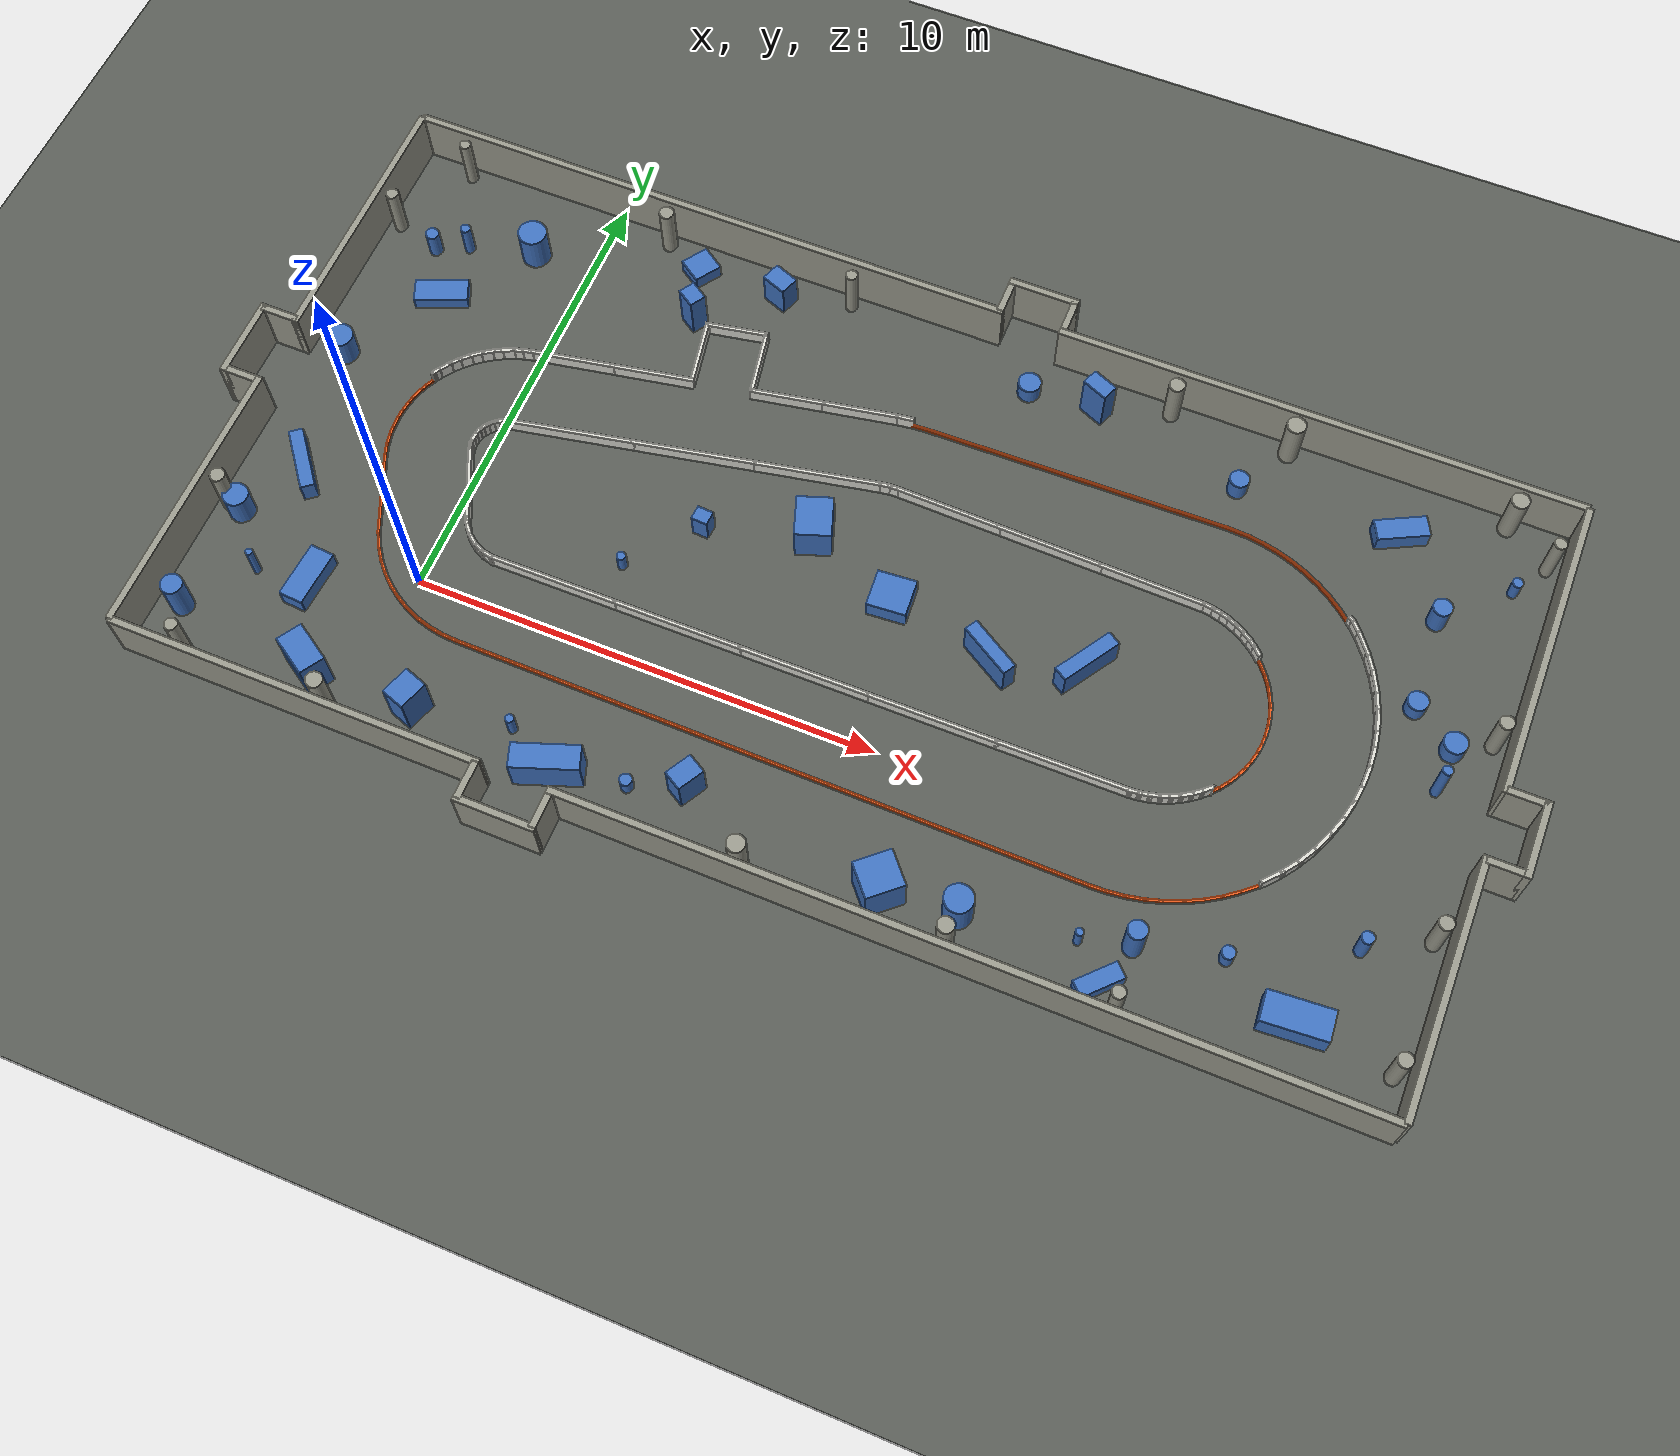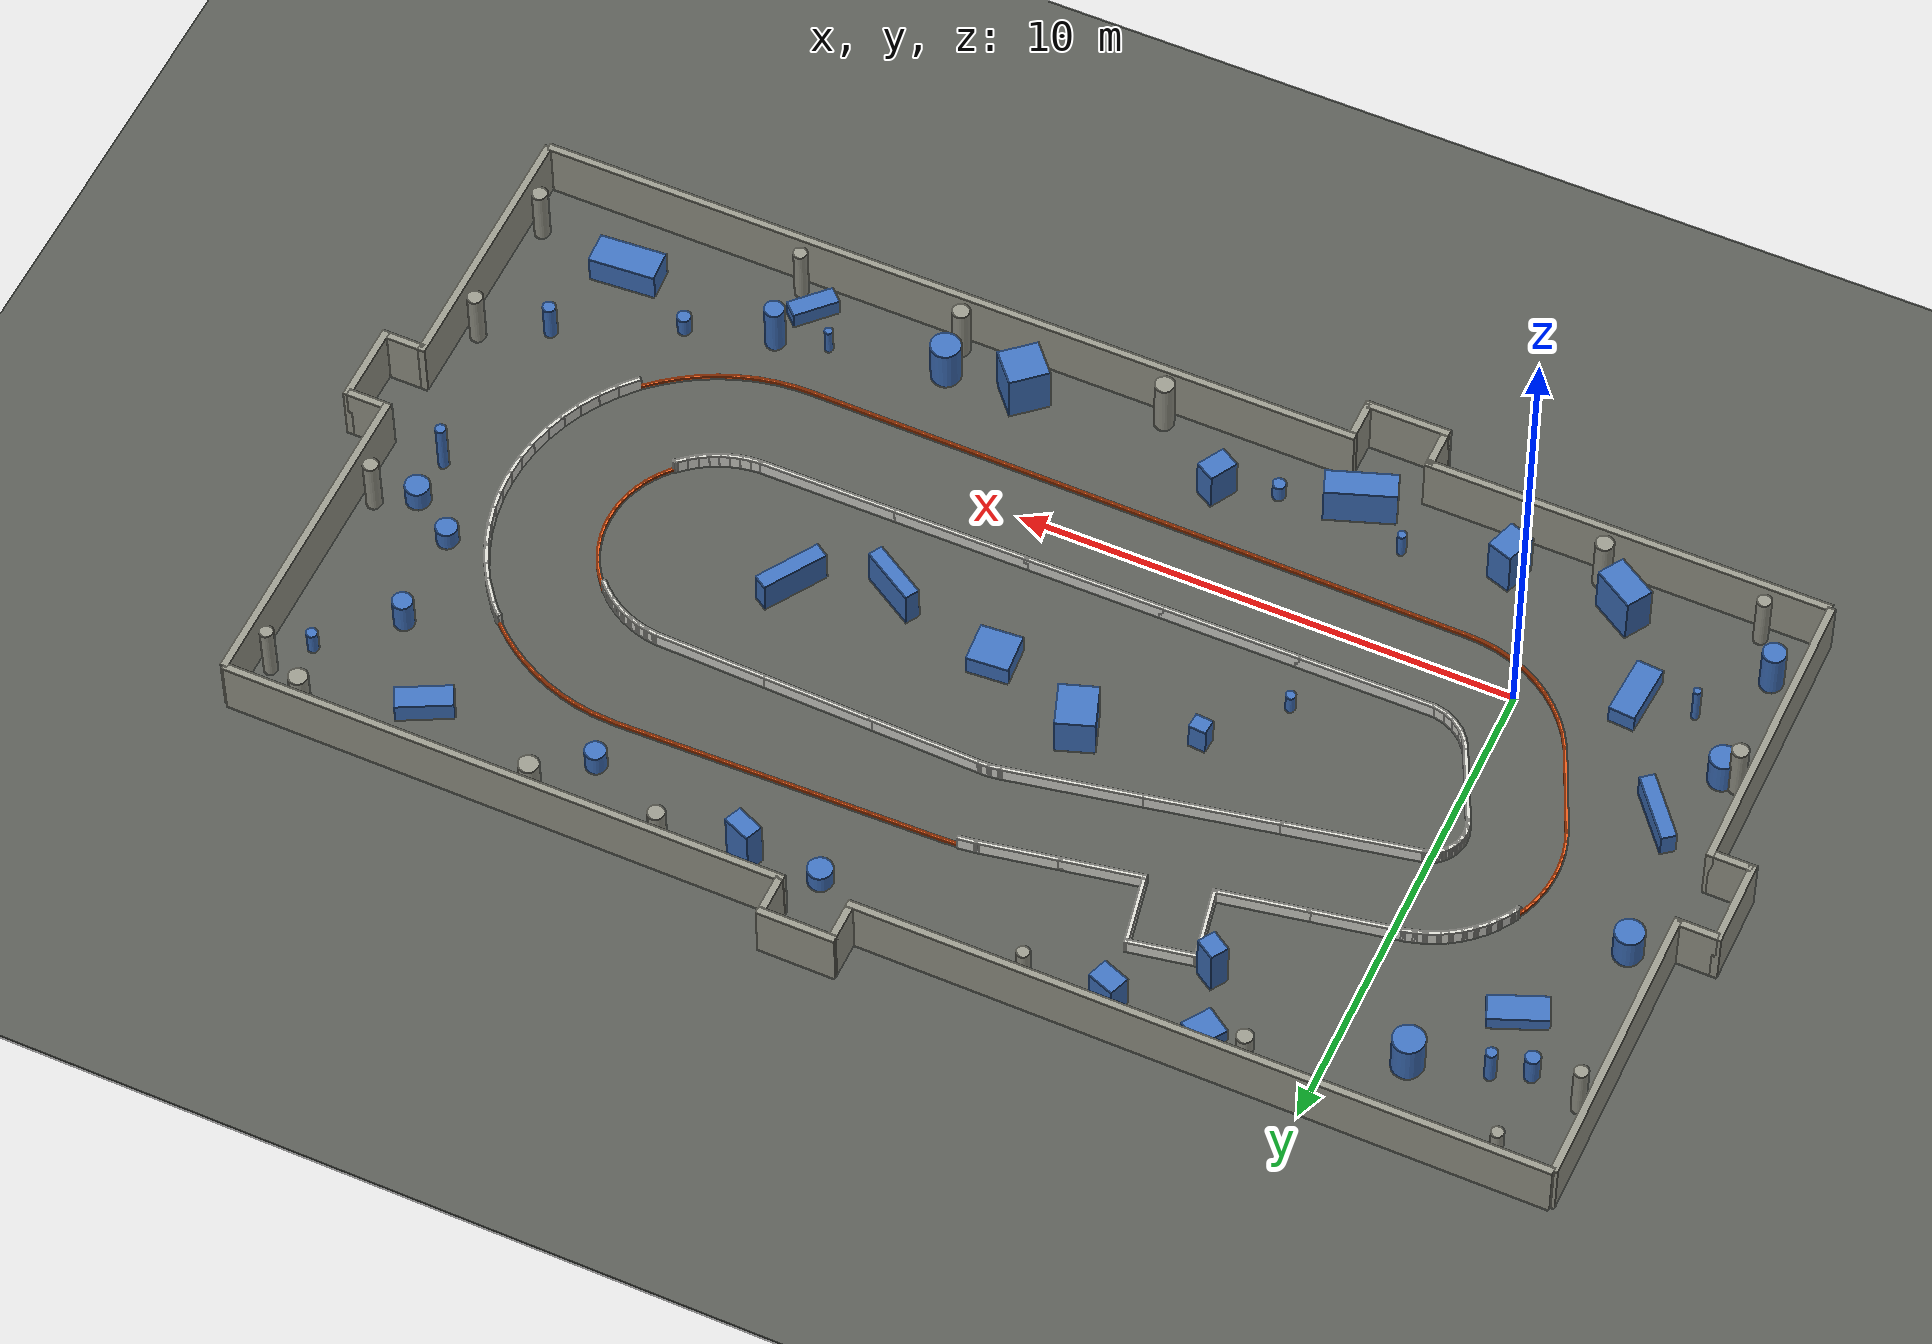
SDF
<?xml version="1.0" ?>
<sdf version="1.9">
  <!-- Generated by simulation/tools/generate_pose_dataset.py --install-gazebo-worlds from tools/pose_dataset/config/tracks.yaml (oval_asym). Do not edit by hand: change the YAML and regenerate. -->
  <world name="default">
    <physics name="default_physics" type="dart">
      <max_step_size>0.001</max_step_size>
      <real_time_factor>1.0</real_time_factor>
      <real_time_update_rate>1000.0</real_time_update_rate>
    </physics>
    <plugin filename="gz-sim-physics-system" name="gz::sim::systems::Physics" />
    <plugin filename="gz-sim-user-commands-system" name="gz::sim::systems::UserCommands" />
    <plugin filename="gz-sim-scene-broadcaster-system" name="gz::sim::systems::SceneBroadcaster" />
    <plugin filename="gz-sim-imu-system" name="gz::sim::systems::Imu" />
    <plugin filename="gz-sim-sensors-system" name="gz::sim::systems::Sensors">
      <render_engine>ogre2</render_engine>
    </plugin>
    <light type="directional" name="sun">
      <pose>0 0 10 0 0 0</pose>
      <diffuse>0.8 0.8 0.8 1</diffuse>
      <direction>-0.5 0.5 -1</direction>
      <cast_shadows>true</cast_shadows>
    </light>
    <model name="track_curb">
      <static>true</static>
      <pose>0 0 0 0 0 0</pose>
      <link name="curb_link">
        <collision name="left0_0_0_collision">
          <pose>16.416032 1.755825 0.035000 0.000000 0.000000 0.841498</pose>
          <geometry>
            <box>
              <size>0.276331 0.060000 0.070000</size>
            </box>
          </geometry>
        </collision>
        <visual name="left0_0_0_visual">
          <pose>16.416032 1.755825 0.035000 0.000000 0.000000 0.841498</pose>
          <geometry>
            <box>
              <size>0.276331 0.060000 0.070000</size>
            </box>
          </geometry>
          <material>
            <ambient>0.9 0.35 0.1 1</ambient>
            <diffuse>0.9 0.35 0.1 1</diffuse>
          </material>
        </visual>
        <collision name="left0_1_0_collision">
          <pose>16.551795 1.923907 0.035000 0.000000 0.000000 0.941231</pose>
          <geometry>
            <box>
              <size>0.276331 0.060000 0.070000</size>
            </box>
          </geometry>
        </collision>
        <visual name="left0_1_0_visual">
          <pose>16.551795 1.923907 0.035000 0.000000 0.000000 0.941231</pose>
          <geometry>
            <box>
              <size>0.276331 0.060000 0.070000</size>
            </box>
          </geometry>
          <material>
            <ambient>0.9 0.35 0.1 1</ambient>
            <diffuse>0.9 0.35 0.1 1</diffuse>
          </material>
        </visual>
        <collision name="left0_2_0_collision">
          <pose>16.670148 2.104670 0.035000 0.000000 0.000000 1.040964</pose>
          <geometry>
            <box>
              <size>0.276331 0.060000 0.070000</size>
            </box>
          </geometry>
        </collision>
        <visual name="left0_2_0_visual">
          <pose>16.670148 2.104670 0.035000 0.000000 0.000000 1.040964</pose>
          <geometry>
            <box>
              <size>0.276331 0.060000 0.070000</size>
            </box>
          </geometry>
          <material>
            <ambient>0.9 0.35 0.1 1</ambient>
            <diffuse>0.9 0.35 0.1 1</diffuse>
          </material>
        </visual>
        <collision name="left0_3_0_collision">
          <pose>16.767385 2.290048 0.035000 0.000000 0.000000 1.137581</pose>
          <geometry>
            <box>
              <size>0.262821 0.060000 0.070000</size>
            </box>
          </geometry>
        </collision>
        <visual name="left0_3_0_visual">
          <pose>16.767385 2.290048 0.035000 0.000000 0.000000 1.137581</pose>
          <geometry>
            <box>
              <size>0.262821 0.060000 0.070000</size>
            </box>
          </geometry>
          <material>
            <ambient>0.9 0.35 0.1 1</ambient>
            <diffuse>0.9 0.35 0.1 1</diffuse>
          </material>
        </visual>
        <collision name="left0_4_0_collision">
          <pose>16.843748 2.477704 0.035000 0.000000 0.000000 1.231080</pose>
          <geometry>
            <box>
              <size>0.262821 0.060000 0.070000</size>
            </box>
          </geometry>
        </collision>
        <visual name="left0_4_0_visual">
          <pose>16.843748 2.477704 0.035000 0.000000 0.000000 1.231080</pose>
          <geometry>
            <box>
              <size>0.262821 0.060000 0.070000</size>
            </box>
          </geometry>
          <material>
            <ambient>0.9 0.35 0.1 1</ambient>
            <diffuse>0.9 0.35 0.1 1</diffuse>
          </material>
        </visual>
        <collision name="left0_5_0_collision">
          <pose>16.903576 2.678304 0.035000 0.000000 0.000000 1.327697</pose>
          <geometry>
            <box>
              <size>0.276331 0.060000 0.070000</size>
            </box>
          </geometry>
        </collision>
        <visual name="left0_5_0_visual">
          <pose>16.903576 2.678304 0.035000 0.000000 0.000000 1.327697</pose>
          <geometry>
            <box>
              <size>0.276331 0.060000 0.070000</size>
            </box>
          </geometry>
          <material>
            <ambient>0.9 0.35 0.1 1</ambient>
            <diffuse>0.9 0.35 0.1 1</diffuse>
          </material>
        </visual>
        <collision name="left0_6_0_collision">
          <pose>16.945067 2.890345 0.035000 0.000000 0.000000 1.427430</pose>
          <geometry>
            <box>
              <size>0.276331 0.060000 0.070000</size>
            </box>
          </geometry>
        </collision>
        <visual name="left0_6_0_visual">
          <pose>16.945067 2.890345 0.035000 0.000000 0.000000 1.427430</pose>
          <geometry>
            <box>
              <size>0.276331 0.060000 0.070000</size>
            </box>
          </geometry>
          <material>
            <ambient>0.9 0.35 0.1 1</ambient>
            <diffuse>0.9 0.35 0.1 1</diffuse>
          </material>
        </visual>
        <collision name="left0_7_0_collision">
          <pose>16.965240 3.105464 0.035000 0.000000 0.000000 1.527163</pose>
          <geometry>
            <box>
              <size>0.276331 0.060000 0.070000</size>
            </box>
          </geometry>
        </collision>
        <visual name="left0_7_0_visual">
          <pose>16.965240 3.105464 0.035000 0.000000 0.000000 1.527163</pose>
          <geometry>
            <box>
              <size>0.276331 0.060000 0.070000</size>
            </box>
          </geometry>
          <material>
            <ambient>0.9 0.35 0.1 1</ambient>
            <diffuse>0.9 0.35 0.1 1</diffuse>
          </material>
        </visual>
        <collision name="left0_8_0_collision">
          <pose>16.963893 3.321522 0.035000 0.000000 0.000000 1.626896</pose>
          <geometry>
            <box>
              <size>0.276331 0.060000 0.070000</size>
            </box>
          </geometry>
        </collision>
        <visual name="left0_8_0_visual">
          <pose>16.963893 3.321522 0.035000 0.000000 0.000000 1.626896</pose>
          <geometry>
            <box>
              <size>0.276331 0.060000 0.070000</size>
            </box>
          </geometry>
          <material>
            <ambient>0.9 0.35 0.1 1</ambient>
            <diffuse>0.9 0.35 0.1 1</diffuse>
          </material>
        </visual>
        <collision name="left0_9_0_collision">
          <pose>16.941040 3.536372 0.035000 0.000000 0.000000 1.726629</pose>
          <geometry>
            <box>
              <size>0.276331 0.060000 0.070000</size>
            </box>
          </geometry>
        </collision>
        <visual name="left0_9_0_visual">
          <pose>16.941040 3.536372 0.035000 0.000000 0.000000 1.726629</pose>
          <geometry>
            <box>
              <size>0.276331 0.060000 0.070000</size>
            </box>
          </geometry>
          <material>
            <ambient>0.9 0.35 0.1 1</ambient>
            <diffuse>0.9 0.35 0.1 1</diffuse>
          </material>
        </visual>
        <collision name="left0_10_0_collision">
          <pose>16.896909 3.747879 0.035000 0.000000 0.000000 1.826362</pose>
          <geometry>
            <box>
              <size>0.276331 0.060000 0.070000</size>
            </box>
          </geometry>
        </collision>
        <visual name="left0_10_0_visual">
          <pose>16.896909 3.747879 0.035000 0.000000 0.000000 1.826362</pose>
          <geometry>
            <box>
              <size>0.276331 0.060000 0.070000</size>
            </box>
          </geometry>
          <material>
            <ambient>0.9 0.35 0.1 1</ambient>
            <diffuse>0.9 0.35 0.1 1</diffuse>
          </material>
        </visual>
        <collision name="left0_11_0_collision">
          <pose>16.831938 3.953941 0.035000 0.000000 0.000000 1.926095</pose>
          <geometry>
            <box>
              <size>0.276331 0.060000 0.070000</size>
            </box>
          </geometry>
        </collision>
        <visual name="left0_11_0_visual">
          <pose>16.831938 3.953941 0.035000 0.000000 0.000000 1.926095</pose>
          <geometry>
            <box>
              <size>0.276331 0.060000 0.070000</size>
            </box>
          </geometry>
          <material>
            <ambient>0.9 0.35 0.1 1</ambient>
            <diffuse>0.9 0.35 0.1 1</diffuse>
          </material>
        </visual>
        <collision name="left0_12_0_collision">
          <pose>16.743483 4.158420 0.035000 0.000000 0.000000 2.028945</pose>
          <geometry>
            <box>
              <size>0.289840 0.060000 0.070000</size>
            </box>
          </geometry>
        </collision>
        <visual name="left0_12_0_visual">
          <pose>16.743483 4.158420 0.035000 0.000000 0.000000 2.028945</pose>
          <geometry>
            <box>
              <size>0.289840 0.060000 0.070000</size>
            </box>
          </geometry>
          <material>
            <ambient>0.9 0.35 0.1 1</ambient>
            <diffuse>0.9 0.35 0.1 1</diffuse>
          </material>
        </visual>
        <collision name="left0_13_0_collision">
          <pose>16.635107 4.353074 0.035000 0.000000 0.000000 2.131795</pose>
          <geometry>
            <box>
              <size>0.276331 0.060000 0.070000</size>
            </box>
          </geometry>
        </collision>
        <visual name="left0_13_0_visual">
          <pose>16.635107 4.353074 0.035000 0.000000 0.000000 2.131795</pose>
          <geometry>
            <box>
              <size>0.276331 0.060000 0.070000</size>
            </box>
          </geometry>
          <material>
            <ambient>0.9 0.35 0.1 1</ambient>
            <diffuse>0.9 0.35 0.1 1</diffuse>
          </material>
        </visual>
        <collision name="left0_14_0_collision">
          <pose>16.502293 4.540260 0.035000 0.000000 0.000000 2.237761</pose>
          <geometry>
            <box>
              <size>0.303346 0.060000 0.070000</size>
            </box>
          </geometry>
        </collision>
        <visual name="left0_14_0_visual">
          <pose>16.502293 4.540260 0.035000 0.000000 0.000000 2.237761</pose>
          <geometry>
            <box>
              <size>0.303346 0.060000 0.070000</size>
            </box>
          </geometry>
          <material>
            <ambient>0.9 0.35 0.1 1</ambient>
            <diffuse>0.9 0.35 0.1 1</diffuse>
          </material>
        </visual>
        <collision name="left0_15_0_collision">
          <pose>16.380723 4.685140 0.035000 0.000000 0.000000 2.325028</pose>
          <geometry>
            <box>
              <size>0.195241 0.060000 0.070000</size>
            </box>
          </geometry>
        </collision>
        <visual name="left0_15_0_visual">
          <pose>16.380723 4.685140 0.035000 0.000000 0.000000 2.325028</pose>
          <geometry>
            <box>
              <size>0.195241 0.060000 0.070000</size>
            </box>
          </geometry>
          <material>
            <ambient>0.9 0.35 0.1 1</ambient>
            <diffuse>0.9 0.35 0.1 1</diffuse>
          </material>
        </visual>
        <collision name="left0_16_0_collision">
          <pose>16.326262 4.735784 0.035000 0.000000 0.000000 2.976192</pose>
          <geometry>
            <box>
              <size>0.076546 0.060000 0.070000</size>
            </box>
          </geometry>
        </collision>
        <visual name="left0_16_0_visual">
          <pose>16.326262 4.735784 0.035000 0.000000 0.000000 2.976192</pose>
          <geometry>
            <box>
              <size>0.076546 0.060000 0.070000</size>
            </box>
          </geometry>
          <material>
            <ambient>0.9 0.35 0.1 1</ambient>
            <diffuse>0.9 0.35 0.1 1</diffuse>
          </material>
        </visual>
        <collision name="right1_0_0_collision">
          <pose>17.643598 6.322559 0.035000 0.000000 0.000000 2.419193</pose>
          <geometry>
            <box>
              <size>0.402461 0.060000 0.070000</size>
            </box>
          </geometry>
        </collision>
        <visual name="right1_0_0_visual">
          <pose>17.643598 6.322559 0.035000 0.000000 0.000000 2.419193</pose>
          <geometry>
            <box>
              <size>0.402461 0.060000 0.070000</size>
            </box>
          </geometry>
          <material>
            <ambient>0.9 0.35 0.1 1</ambient>
            <diffuse>0.9 0.35 0.1 1</diffuse>
          </material>
        </visual>
        <collision name="right1_1_0_collision">
          <pose>17.378112 6.538082 0.035000 0.000000 0.000000 2.500248</pose>
          <geometry>
            <box>
              <size>0.402010 0.060000 0.070000</size>
            </box>
          </geometry>
        </collision>
        <visual name="right1_1_0_visual">
          <pose>17.378112 6.538082 0.035000 0.000000 0.000000 2.500248</pose>
          <geometry>
            <box>
              <size>0.402010 0.060000 0.070000</size>
            </box>
          </geometry>
          <material>
            <ambient>0.9 0.35 0.1 1</ambient>
            <diffuse>0.9 0.35 0.1 1</diffuse>
          </material>
        </visual>
        <collision name="right1_2_0_collision">
          <pose>17.096419 6.731147 0.035000 0.000000 0.000000 2.581303</pose>
          <geometry>
            <box>
              <size>0.401559 0.060000 0.070000</size>
            </box>
          </geometry>
        </collision>
        <visual name="right1_2_0_visual">
          <pose>17.096419 6.731147 0.035000 0.000000 0.000000 2.581303</pose>
          <geometry>
            <box>
              <size>0.401559 0.060000 0.070000</size>
            </box>
          </geometry>
          <material>
            <ambient>0.9 0.35 0.1 1</ambient>
            <diffuse>0.9 0.35 0.1 1</diffuse>
          </material>
        </visual>
        <collision name="right1_3_0_collision">
          <pose>16.788521 6.906081 0.035000 0.000000 0.000000 2.665473</pose>
          <geometry>
            <box>
              <size>0.427312 0.060000 0.070000</size>
            </box>
          </geometry>
        </collision>
        <visual name="right1_3_0_visual">
          <pose>16.788521 6.906081 0.035000 0.000000 0.000000 2.665473</pose>
          <geometry>
            <box>
              <size>0.427312 0.060000 0.070000</size>
            </box>
          </geometry>
          <material>
            <ambient>0.9 0.35 0.1 1</ambient>
            <diffuse>0.9 0.35 0.1 1</diffuse>
          </material>
        </visual>
        <collision name="right1_4_0_collision">
          <pose>16.467895 7.055313 0.035000 0.000000 0.000000 2.749647</pose>
          <geometry>
            <box>
              <size>0.400622 0.060000 0.070000</size>
            </box>
          </geometry>
        </collision>
        <visual name="right1_4_0_visual">
          <pose>16.467895 7.055313 0.035000 0.000000 0.000000 2.749647</pose>
          <geometry>
            <box>
              <size>0.400622 0.060000 0.070000</size>
            </box>
          </geometry>
          <material>
            <ambient>0.9 0.35 0.1 1</ambient>
            <diffuse>0.9 0.35 0.1 1</diffuse>
          </material>
        </visual>
        <collision name="right1_5_0_collision">
          <pose>16.148567 7.172400 0.035000 0.000000 0.000000 2.830702</pose>
          <geometry>
            <box>
              <size>0.400171 0.060000 0.070000</size>
            </box>
          </geometry>
        </collision>
        <visual name="right1_5_0_visual">
          <pose>16.148567 7.172400 0.035000 0.000000 0.000000 2.830702</pose>
          <geometry>
            <box>
              <size>0.400171 0.060000 0.070000</size>
            </box>
          </geometry>
          <material>
            <ambient>0.9 0.35 0.1 1</ambient>
            <diffuse>0.9 0.35 0.1 1</diffuse>
          </material>
        </visual>
        <collision name="right1_6_0_collision">
          <pose>15.821242 7.263128 0.035000 0.000000 0.000000 2.911757</pose>
          <geometry>
            <box>
              <size>0.399720 0.060000 0.070000</size>
            </box>
          </geometry>
        </collision>
        <visual name="right1_6_0_visual">
          <pose>15.821242 7.263128 0.035000 0.000000 0.000000 2.911757</pose>
          <geometry>
            <box>
              <size>0.399720 0.060000 0.070000</size>
            </box>
          </geometry>
          <material>
            <ambient>0.9 0.35 0.1 1</ambient>
            <diffuse>0.9 0.35 0.1 1</diffuse>
          </material>
        </visual>
        <collision name="right1_7_0_collision">
          <pose>15.475117 7.328339 0.035000 0.000000 0.000000 2.995928</pose>
          <geometry>
            <box>
              <size>0.425332 0.060000 0.070000</size>
            </box>
          </geometry>
        </collision>
        <visual name="right1_7_0_visual">
          <pose>15.475117 7.328339 0.035000 0.000000 0.000000 2.995928</pose>
          <geometry>
            <box>
              <size>0.425332 0.060000 0.070000</size>
            </box>
          </geometry>
          <material>
            <ambient>0.9 0.35 0.1 1</ambient>
            <diffuse>0.9 0.35 0.1 1</diffuse>
          </material>
        </visual>
        <collision name="right1_8_0_collision">
          <pose>15.047952 7.365438 0.035000 0.000000 0.000000 3.098667</pose>
          <geometry>
            <box>
              <size>0.553321 0.060000 0.070000</size>
            </box>
          </geometry>
        </collision>
        <visual name="right1_8_0_visual">
          <pose>15.047952 7.365438 0.035000 0.000000 0.000000 3.098667</pose>
          <geometry>
            <box>
              <size>0.553321 0.060000 0.070000</size>
            </box>
          </geometry>
          <material>
            <ambient>0.9 0.35 0.1 1</ambient>
            <diffuse>0.9 0.35 0.1 1</diffuse>
          </material>
        </visual>
        <collision name="right1_9_0_collision">
          <pose>13.710873 7.352611 0.035000 0.000000 0.000000 -3.120130</pose>
          <geometry>
            <box>
              <size>2.241796 0.060000 0.070000</size>
            </box>
          </geometry>
        </collision>
        <visual name="right1_9_0_visual">
          <pose>13.710873 7.352611 0.035000 0.000000 0.000000 -3.120130</pose>
          <geometry>
            <box>
              <size>2.241796 0.060000 0.070000</size>
            </box>
          </geometry>
          <material>
            <ambient>0.9 0.35 0.1 1</ambient>
            <diffuse>0.9 0.35 0.1 1</diffuse>
          </material>
        </visual>
        <collision name="right1_9_1_collision">
          <pose>11.529579 7.305787 0.035000 0.000000 0.000000 -3.120130</pose>
          <geometry>
            <box>
              <size>2.241796 0.060000 0.070000</size>
            </box>
          </geometry>
        </collision>
        <visual name="right1_9_1_visual">
          <pose>11.529579 7.305787 0.035000 0.000000 0.000000 -3.120130</pose>
          <geometry>
            <box>
              <size>2.241796 0.060000 0.070000</size>
            </box>
          </geometry>
          <material>
            <ambient>0.9 0.35 0.1 1</ambient>
            <diffuse>0.9 0.35 0.1 1</diffuse>
          </material>
        </visual>
        <collision name="right1_9_2_collision">
          <pose>9.348286 7.258963 0.035000 0.000000 0.000000 -3.120130</pose>
          <geometry>
            <box>
              <size>2.241796 0.060000 0.070000</size>
            </box>
          </geometry>
        </collision>
        <visual name="right1_9_2_visual">
          <pose>9.348286 7.258963 0.035000 0.000000 0.000000 -3.120130</pose>
          <geometry>
            <box>
              <size>2.241796 0.060000 0.070000</size>
            </box>
          </geometry>
          <material>
            <ambient>0.9 0.35 0.1 1</ambient>
            <diffuse>0.9 0.35 0.1 1</diffuse>
          </material>
        </visual>
        <collision name="right1_10_0_collision">
          <pose>8.096702 7.225018 0.035000 0.000000 0.000000 -3.076235</pose>
          <geometry>
            <box>
              <size>0.382564 0.060000 0.070000</size>
            </box>
          </geometry>
        </collision>
        <visual name="right1_10_0_visual">
          <pose>8.096702 7.225018 0.035000 0.000000 0.000000 -3.076235</pose>
          <geometry>
            <box>
              <size>0.382564 0.060000 0.070000</size>
            </box>
          </geometry>
          <material>
            <ambient>0.9 0.35 0.1 1</ambient>
            <diffuse>0.9 0.35 0.1 1</diffuse>
          </material>
        </visual>
        <collision name="right1_11_0_collision">
          <pose>7.922942 7.218220 0.035000 0.000000 0.000000 2.858123</pose>
          <geometry>
            <box>
              <size>0.086710 0.060000 0.070000</size>
            </box>
          </geometry>
        </collision>
        <visual name="right1_11_0_visual">
          <pose>7.922942 7.218220 0.035000 0.000000 0.000000 2.858123</pose>
          <geometry>
            <box>
              <size>0.086710 0.060000 0.070000</size>
            </box>
          </geometry>
          <material>
            <ambient>0.9 0.35 0.1 1</ambient>
            <diffuse>0.9 0.35 0.1 1</diffuse>
          </material>
        </visual>
        <collision name="right5_0_0_collision">
          <pose>-1.968130 4.344300 0.035000 0.000000 0.000000 -2.011185</pose>
          <geometry>
            <box>
              <size>0.275675 0.060000 0.070000</size>
            </box>
          </geometry>
        </collision>
        <visual name="right5_0_0_visual">
          <pose>-1.968130 4.344300 0.035000 0.000000 0.000000 -2.011185</pose>
          <geometry>
            <box>
              <size>0.275675 0.060000 0.070000</size>
            </box>
          </geometry>
          <material>
            <ambient>0.9 0.35 0.1 1</ambient>
            <diffuse>0.9 0.35 0.1 1</diffuse>
          </material>
        </visual>
        <collision name="right5_1_0_collision">
          <pose>-2.046653 4.160172 0.035000 0.000000 0.000000 -1.930436</pose>
          <geometry>
            <box>
              <size>0.244994 0.060000 0.070000</size>
            </box>
          </geometry>
        </collision>
        <visual name="right5_1_0_visual">
          <pose>-2.046653 4.160172 0.035000 0.000000 0.000000 -1.930436</pose>
          <geometry>
            <box>
              <size>0.244994 0.060000 0.070000</size>
            </box>
          </geometry>
          <material>
            <ambient>0.9 0.35 0.1 1</ambient>
            <diffuse>0.9 0.35 0.1 1</diffuse>
          </material>
        </visual>
        <collision name="right5_2_0_collision">
          <pose>-2.108929 3.969793 0.035000 0.000000 0.000000 -1.849683</pose>
          <geometry>
            <box>
              <size>0.275942 0.060000 0.070000</size>
            </box>
          </geometry>
        </collision>
        <visual name="right5_2_0_visual">
          <pose>-2.108929 3.969793 0.035000 0.000000 0.000000 -1.849683</pose>
          <geometry>
            <box>
              <size>0.275942 0.060000 0.070000</size>
            </box>
          </geometry>
          <material>
            <ambient>0.9 0.35 0.1 1</ambient>
            <diffuse>0.9 0.35 0.1 1</diffuse>
          </material>
        </visual>
        <collision name="right5_3_0_collision">
          <pose>-2.156882 3.775194 0.035000 0.000000 0.000000 -1.768934</pose>
          <geometry>
            <box>
              <size>0.245223 0.060000 0.070000</size>
            </box>
          </geometry>
        </collision>
        <visual name="right5_3_0_visual">
          <pose>-2.156882 3.775194 0.035000 0.000000 0.000000 -1.768934</pose>
          <geometry>
            <box>
              <size>0.245223 0.060000 0.070000</size>
            </box>
          </geometry>
          <material>
            <ambient>0.9 0.35 0.1 1</ambient>
            <diffuse>0.9 0.35 0.1 1</diffuse>
          </material>
        </visual>
        <collision name="right5_4_0_collision">
          <pose>-2.187773 3.577034 0.035000 0.000000 0.000000 -1.688182</pose>
          <geometry>
            <box>
              <size>0.276210 0.060000 0.070000</size>
            </box>
          </geometry>
        </collision>
        <visual name="right5_4_0_visual">
          <pose>-2.187773 3.577034 0.035000 0.000000 0.000000 -1.688182</pose>
          <geometry>
            <box>
              <size>0.276210 0.060000 0.070000</size>
            </box>
          </geometry>
          <material>
            <ambient>0.9 0.35 0.1 1</ambient>
            <diffuse>0.9 0.35 0.1 1</diffuse>
          </material>
        </visual>
        <collision name="right5_5_0_collision">
          <pose>-2.203830 3.377009 0.035000 0.000000 0.000000 -1.607432</pose>
          <geometry>
            <box>
              <size>0.245453 0.060000 0.070000</size>
            </box>
          </geometry>
        </collision>
        <visual name="right5_5_0_visual">
          <pose>-2.203830 3.377009 0.035000 0.000000 0.000000 -1.607432</pose>
          <geometry>
            <box>
              <size>0.245453 0.060000 0.070000</size>
            </box>
          </geometry>
          <material>
            <ambient>0.9 0.35 0.1 1</ambient>
            <diffuse>0.9 0.35 0.1 1</diffuse>
          </material>
        </visual>
        <collision name="right5_6_0_collision">
          <pose>-2.202453 3.176211 0.035000 0.000000 0.000000 -1.526680</pose>
          <geometry>
            <box>
              <size>0.276477 0.060000 0.070000</size>
            </box>
          </geometry>
        </collision>
        <visual name="right5_6_0_visual">
          <pose>-2.202453 3.176211 0.035000 0.000000 0.000000 -1.526680</pose>
          <geometry>
            <box>
              <size>0.276477 0.060000 0.070000</size>
            </box>
          </geometry>
          <material>
            <ambient>0.9 0.35 0.1 1</ambient>
            <diffuse>0.9 0.35 0.1 1</diffuse>
          </material>
        </visual>
        <collision name="right5_7_0_collision">
          <pose>-2.186117 2.975960 0.035000 0.000000 0.000000 -1.445931</pose>
          <geometry>
            <box>
              <size>0.245682 0.060000 0.070000</size>
            </box>
          </geometry>
        </collision>
        <visual name="right5_7_0_visual">
          <pose>-2.186117 2.975960 0.035000 0.000000 0.000000 -1.445931</pose>
          <geometry>
            <box>
              <size>0.245682 0.060000 0.070000</size>
            </box>
          </geometry>
          <material>
            <ambient>0.9 0.35 0.1 1</ambient>
            <diffuse>0.9 0.35 0.1 1</diffuse>
          </material>
        </visual>
        <collision name="right5_8_0_collision">
          <pose>-2.144416 2.747820 0.035000 0.000000 0.000000 -1.352752</pose>
          <geometry>
            <box>
              <size>0.338641 0.060000 0.070000</size>
            </box>
          </geometry>
        </collision>
        <visual name="right5_8_0_visual">
          <pose>-2.144416 2.747820 0.035000 0.000000 0.000000 -1.352752</pose>
          <geometry>
            <box>
              <size>0.338641 0.060000 0.070000</size>
            </box>
          </geometry>
          <material>
            <ambient>0.9 0.35 0.1 1</ambient>
            <diffuse>0.9 0.35 0.1 1</diffuse>
          </material>
        </visual>
        <collision name="right5_9_0_collision">
          <pose>-2.074859 2.494280 0.035000 0.000000 0.000000 -1.247157</pose>
          <geometry>
            <box>
              <size>0.307907 0.060000 0.070000</size>
            </box>
          </geometry>
        </collision>
        <visual name="right5_9_0_visual">
          <pose>-2.074859 2.494280 0.035000 0.000000 0.000000 -1.247157</pose>
          <geometry>
            <box>
              <size>0.307907 0.060000 0.070000</size>
            </box>
          </geometry>
          <material>
            <ambient>0.9 0.35 0.1 1</ambient>
            <diffuse>0.9 0.35 0.1 1</diffuse>
          </material>
        </visual>
        <collision name="right5_10_0_collision">
          <pose>-1.669785 1.530469 0.035000 0.000000 0.000000 -1.162956</pose>
          <geometry>
            <box>
              <size>1.903815 0.060000 0.070000</size>
            </box>
          </geometry>
        </collision>
        <visual name="right5_10_0_visual">
          <pose>-1.669785 1.530469 0.035000 0.000000 0.000000 -1.162956</pose>
          <geometry>
            <box>
              <size>1.903815 0.060000 0.070000</size>
            </box>
          </geometry>
          <material>
            <ambient>0.9 0.35 0.1 1</ambient>
            <diffuse>0.9 0.35 0.1 1</diffuse>
          </material>
        </visual>
        <collision name="right5_11_0_collision">
          <pose>-1.217812 0.533197 0.035000 0.000000 0.000000 -1.051425</pose>
          <geometry>
            <box>
              <size>0.407828 0.060000 0.070000</size>
            </box>
          </geometry>
        </collision>
        <visual name="right5_11_0_visual">
          <pose>-1.217812 0.533197 0.035000 0.000000 0.000000 -1.051425</pose>
          <geometry>
            <box>
              <size>0.407828 0.060000 0.070000</size>
            </box>
          </geometry>
          <material>
            <ambient>0.9 0.35 0.1 1</ambient>
            <diffuse>0.9 0.35 0.1 1</diffuse>
          </material>
        </visual>
        <collision name="right5_12_0_collision">
          <pose>-1.037005 0.253611 0.035000 0.000000 0.000000 -0.937155</pose>
          <geometry>
            <box>
              <size>0.379170 0.060000 0.070000</size>
            </box>
          </geometry>
        </collision>
        <visual name="right5_12_0_visual">
          <pose>-1.037005 0.253611 0.035000 0.000000 0.000000 -0.937155</pose>
          <geometry>
            <box>
              <size>0.379170 0.060000 0.070000</size>
            </box>
          </geometry>
          <material>
            <ambient>0.9 0.35 0.1 1</ambient>
            <diffuse>0.9 0.35 0.1 1</diffuse>
          </material>
        </visual>
        <collision name="right5_13_0_collision">
          <pose>-0.834469 0.007369 0.035000 0.000000 0.000000 -0.827852</pose>
          <geometry>
            <box>
              <size>0.379454 0.060000 0.070000</size>
            </box>
          </geometry>
        </collision>
        <visual name="right5_13_0_visual">
          <pose>-0.834469 0.007369 0.035000 0.000000 0.000000 -0.827852</pose>
          <geometry>
            <box>
              <size>0.379454 0.060000 0.070000</size>
            </box>
          </geometry>
          <material>
            <ambient>0.9 0.35 0.1 1</ambient>
            <diffuse>0.9 0.35 0.1 1</diffuse>
          </material>
        </visual>
        <collision name="right5_14_0_collision">
          <pose>-0.606077 -0.215507 0.035000 0.000000 0.000000 -0.718549</pose>
          <geometry>
            <box>
              <size>0.379738 0.060000 0.070000</size>
            </box>
          </geometry>
        </collision>
        <visual name="right5_14_0_visual">
          <pose>-0.606077 -0.215507 0.035000 0.000000 0.000000 -0.718549</pose>
          <geometry>
            <box>
              <size>0.379738 0.060000 0.070000</size>
            </box>
          </geometry>
          <material>
            <ambient>0.9 0.35 0.1 1</ambient>
            <diffuse>0.9 0.35 0.1 1</diffuse>
          </material>
        </visual>
        <collision name="right5_15_0_collision">
          <pose>-0.354417 -0.412160 0.035000 0.000000 0.000000 -0.608117</pose>
          <geometry>
            <box>
              <size>0.380000 0.060000 0.070000</size>
            </box>
          </geometry>
        </collision>
        <visual name="right5_15_0_visual">
          <pose>-0.354417 -0.412160 0.035000 0.000000 0.000000 -0.608117</pose>
          <geometry>
            <box>
              <size>0.380000 0.060000 0.070000</size>
            </box>
          </geometry>
          <material>
            <ambient>0.9 0.35 0.1 1</ambient>
            <diffuse>0.9 0.35 0.1 1</diffuse>
          </material>
        </visual>
        <collision name="right5_16_0_collision">
          <pose>-0.082285 -0.579734 0.035000 0.000000 0.000000 -0.495801</pose>
          <geometry>
            <box>
              <size>0.380187 0.060000 0.070000</size>
            </box>
          </geometry>
        </collision>
        <visual name="right5_16_0_visual">
          <pose>-0.082285 -0.579734 0.035000 0.000000 0.000000 -0.495801</pose>
          <geometry>
            <box>
              <size>0.380187 0.060000 0.070000</size>
            </box>
          </geometry>
          <material>
            <ambient>0.9 0.35 0.1 1</ambient>
            <diffuse>0.9 0.35 0.1 1</diffuse>
          </material>
        </visual>
        <collision name="right5_17_0_collision">
          <pose>0.220679 -0.720949 0.035000 0.000000 0.000000 -0.381535</pose>
          <geometry>
            <box>
              <size>0.409420 0.060000 0.070000</size>
            </box>
          </geometry>
        </collision>
        <visual name="right5_17_0_visual">
          <pose>0.220679 -0.720949 0.035000 0.000000 0.000000 -0.381535</pose>
          <geometry>
            <box>
              <size>0.409420 0.060000 0.070000</size>
            </box>
          </geometry>
          <material>
            <ambient>0.9 0.35 0.1 1</ambient>
            <diffuse>0.9 0.35 0.1 1</diffuse>
          </material>
        </visual>
        <collision name="right5_18_0_collision">
          <pose>0.537376 -0.828320 0.035000 0.000000 0.000000 -0.267271</pose>
          <geometry>
            <box>
              <size>0.380478 0.060000 0.070000</size>
            </box>
          </geometry>
        </collision>
        <visual name="right5_18_0_visual">
          <pose>0.537376 -0.828320 0.035000 0.000000 0.000000 -0.267271</pose>
          <geometry>
            <box>
              <size>0.380478 0.060000 0.070000</size>
            </box>
          </geometry>
          <material>
            <ambient>0.9 0.35 0.1 1</ambient>
            <diffuse>0.9 0.35 0.1 1</diffuse>
          </material>
        </visual>
        <collision name="right5_19_0_collision">
          <pose>0.835740 -0.894282 0.035000 0.000000 0.000000 -0.162942</pose>
          <geometry>
            <box>
              <size>0.351489 0.060000 0.070000</size>
            </box>
          </geometry>
        </collision>
        <visual name="right5_19_0_visual">
          <pose>0.835740 -0.894282 0.035000 0.000000 0.000000 -0.162942</pose>
          <geometry>
            <box>
              <size>0.351489 0.060000 0.070000</size>
            </box>
          </geometry>
          <material>
            <ambient>0.9 0.35 0.1 1</ambient>
            <diffuse>0.9 0.35 0.1 1</diffuse>
          </material>
        </visual>
        <collision name="right5_20_0_collision">
          <pose>1.138489 -0.927318 0.035000 0.000000 0.000000 -0.059030</pose>
          <geometry>
            <box>
              <size>0.378426 0.060000 0.070000</size>
            </box>
          </geometry>
        </collision>
        <visual name="right5_20_0_visual">
          <pose>1.138489 -0.927318 0.035000 0.000000 0.000000 -0.059030</pose>
          <geometry>
            <box>
              <size>0.378426 0.060000 0.070000</size>
            </box>
          </geometry>
          <material>
            <ambient>0.9 0.35 0.1 1</ambient>
            <diffuse>0.9 0.35 0.1 1</diffuse>
          </material>
        </visual>
        <collision name="right5_21_0_collision">
          <pose>2.647841 -0.944576 0.035000 0.000000 0.000000 -0.005824</pose>
          <geometry>
            <box>
              <size>2.760877 0.060000 0.070000</size>
            </box>
          </geometry>
        </collision>
        <visual name="right5_21_0_visual">
          <pose>2.647841 -0.944576 0.035000 0.000000 0.000000 -0.005824</pose>
          <geometry>
            <box>
              <size>2.760877 0.060000 0.070000</size>
            </box>
          </geometry>
          <material>
            <ambient>0.9 0.35 0.1 1</ambient>
            <diffuse>0.9 0.35 0.1 1</diffuse>
          </material>
        </visual>
        <collision name="right5_21_1_collision">
          <pose>5.348672 -0.960305 0.035000 0.000000 0.000000 -0.005824</pose>
          <geometry>
            <box>
              <size>2.760877 0.060000 0.070000</size>
            </box>
          </geometry>
        </collision>
        <visual name="right5_21_1_visual">
          <pose>5.348672 -0.960305 0.035000 0.000000 0.000000 -0.005824</pose>
          <geometry>
            <box>
              <size>2.760877 0.060000 0.070000</size>
            </box>
          </geometry>
          <material>
            <ambient>0.9 0.35 0.1 1</ambient>
            <diffuse>0.9 0.35 0.1 1</diffuse>
          </material>
        </visual>
        <collision name="right5_21_2_collision">
          <pose>8.049503 -0.976034 0.035000 0.000000 0.000000 -0.005824</pose>
          <geometry>
            <box>
              <size>2.760877 0.060000 0.070000</size>
            </box>
          </geometry>
        </collision>
        <visual name="right5_21_2_visual">
          <pose>8.049503 -0.976034 0.035000 0.000000 0.000000 -0.005824</pose>
          <geometry>
            <box>
              <size>2.760877 0.060000 0.070000</size>
            </box>
          </geometry>
          <material>
            <ambient>0.9 0.35 0.1 1</ambient>
            <diffuse>0.9 0.35 0.1 1</diffuse>
          </material>
        </visual>
        <collision name="right5_21_3_collision">
          <pose>10.750334 -0.991764 0.035000 0.000000 0.000000 -0.005824</pose>
          <geometry>
            <box>
              <size>2.760877 0.060000 0.070000</size>
            </box>
          </geometry>
        </collision>
        <visual name="right5_21_3_visual">
          <pose>10.750334 -0.991764 0.035000 0.000000 0.000000 -0.005824</pose>
          <geometry>
            <box>
              <size>2.760877 0.060000 0.070000</size>
            </box>
          </geometry>
          <material>
            <ambient>0.9 0.35 0.1 1</ambient>
            <diffuse>0.9 0.35 0.1 1</diffuse>
          </material>
        </visual>
        <collision name="right5_21_4_collision">
          <pose>13.451166 -1.007493 0.035000 0.000000 0.000000 -0.005824</pose>
          <geometry>
            <box>
              <size>2.760877 0.060000 0.070000</size>
            </box>
          </geometry>
        </collision>
        <visual name="right5_21_4_visual">
          <pose>13.451166 -1.007493 0.035000 0.000000 0.000000 -0.005824</pose>
          <geometry>
            <box>
              <size>2.760877 0.060000 0.070000</size>
            </box>
          </geometry>
          <material>
            <ambient>0.9 0.35 0.1 1</ambient>
            <diffuse>0.9 0.35 0.1 1</diffuse>
          </material>
        </visual>
        <collision name="right5_22_0_collision">
          <pose>14.945237 -1.011043 0.035000 0.000000 0.000000 0.030023</pose>
          <geometry>
            <box>
              <size>0.347442 0.060000 0.070000</size>
            </box>
          </geometry>
        </collision>
        <visual name="right5_22_0_visual">
          <pose>14.945237 -1.011043 0.035000 0.000000 0.000000 0.030023</pose>
          <geometry>
            <box>
              <size>0.347442 0.060000 0.070000</size>
            </box>
          </geometry>
          <material>
            <ambient>0.9 0.35 0.1 1</ambient>
            <diffuse>0.9 0.35 0.1 1</diffuse>
          </material>
        </visual>
        <collision name="right5_23_0_collision">
          <pose>15.284781 -0.984916 0.035000 0.000000 0.000000 0.110900</pose>
          <geometry>
            <box>
              <size>0.454196 0.060000 0.070000</size>
            </box>
          </geometry>
        </collision>
        <visual name="right5_23_0_visual">
          <pose>15.284781 -0.984916 0.035000 0.000000 0.000000 0.110900</pose>
          <geometry>
            <box>
              <size>0.454196 0.060000 0.070000</size>
            </box>
          </geometry>
          <material>
            <ambient>0.9 0.35 0.1 1</ambient>
            <diffuse>0.9 0.35 0.1 1</diffuse>
          </material>
        </visual>
        <collision name="right5_24_0_collision">
          <pose>15.660993 -0.926308 0.035000 0.000000 0.000000 0.201284</pose>
          <geometry>
            <box>
              <size>0.428081 0.060000 0.070000</size>
            </box>
          </geometry>
        </collision>
        <visual name="right5_24_0_visual">
          <pose>15.660993 -0.926308 0.035000 0.000000 0.000000 0.201284</pose>
          <geometry>
            <box>
              <size>0.428081 0.060000 0.070000</size>
            </box>
          </geometry>
          <material>
            <ambient>0.9 0.35 0.1 1</ambient>
            <diffuse>0.9 0.35 0.1 1</diffuse>
          </material>
        </visual>
        <collision name="right5_25_0_collision">
          <pose>16.030243 -0.832792 0.035000 0.000000 0.000000 0.291669</pose>
          <geometry>
            <box>
              <size>0.454511 0.060000 0.070000</size>
            </box>
          </geometry>
        </collision>
        <visual name="right5_25_0_visual">
          <pose>16.030243 -0.832792 0.035000 0.000000 0.000000 0.291669</pose>
          <geometry>
            <box>
              <size>0.454511 0.060000 0.070000</size>
            </box>
          </geometry>
          <material>
            <ambient>0.9 0.35 0.1 1</ambient>
            <diffuse>0.9 0.35 0.1 1</diffuse>
          </material>
        </visual>
        <collision name="right5_26_0_collision">
          <pose>16.390075 -0.707401 0.035000 0.000000 0.000000 0.382054</pose>
          <geometry>
            <box>
              <size>0.428375 0.060000 0.070000</size>
            </box>
          </geometry>
        </collision>
        <visual name="right5_26_0_visual">
          <pose>16.390075 -0.707401 0.035000 0.000000 0.000000 0.382054</pose>
          <geometry>
            <box>
              <size>0.428375 0.060000 0.070000</size>
            </box>
          </geometry>
          <material>
            <ambient>0.9 0.35 0.1 1</ambient>
            <diffuse>0.9 0.35 0.1 1</diffuse>
          </material>
        </visual>
        <collision name="right5_27_0_collision">
          <pose>16.725318 -0.555394 0.035000 0.000000 0.000000 0.469322</pose>
          <geometry>
            <box>
              <size>0.428517 0.060000 0.070000</size>
            </box>
          </geometry>
        </collision>
        <visual name="right5_27_0_visual">
          <pose>16.725318 -0.555394 0.035000 0.000000 0.000000 0.469322</pose>
          <geometry>
            <box>
              <size>0.428517 0.060000 0.070000</size>
            </box>
          </geometry>
          <material>
            <ambient>0.9 0.35 0.1 1</ambient>
            <diffuse>0.9 0.35 0.1 1</diffuse>
          </material>
        </visual>
        <collision name="right5_28_0_collision">
          <pose>17.046160 -0.374677 0.035000 0.000000 0.000000 0.556590</pose>
          <geometry>
            <box>
              <size>0.428659 0.060000 0.070000</size>
            </box>
          </geometry>
        </collision>
        <visual name="right5_28_0_visual">
          <pose>17.046160 -0.374677 0.035000 0.000000 0.000000 0.556590</pose>
          <geometry>
            <box>
              <size>0.428659 0.060000 0.070000</size>
            </box>
          </geometry>
          <material>
            <ambient>0.9 0.35 0.1 1</ambient>
            <diffuse>0.9 0.35 0.1 1</diffuse>
          </material>
        </visual>
        <collision name="right5_29_0_collision">
          <pose>17.339937 -0.174935 0.035000 0.000000 0.000000 0.640741</pose>
          <geometry>
            <box>
              <size>0.402468 0.060000 0.070000</size>
            </box>
          </geometry>
        </collision>
        <visual name="right5_29_0_visual">
          <pose>17.339937 -0.174935 0.035000 0.000000 0.000000 0.640741</pose>
          <geometry>
            <box>
              <size>0.402468 0.060000 0.070000</size>
            </box>
          </geometry>
          <material>
            <ambient>0.9 0.35 0.1 1</ambient>
            <diffuse>0.9 0.35 0.1 1</diffuse>
          </material>
        </visual>
        <collision name="right5_30_0_collision">
          <pose>17.646985 0.074020 0.035000 0.000000 0.000000 0.712247</pose>
          <geometry>
            <box>
              <size>0.508616 0.060000 0.070000</size>
            </box>
          </geometry>
        </collision>
        <visual name="right5_30_0_visual">
          <pose>17.646985 0.074020 0.035000 0.000000 0.000000 0.712247</pose>
          <geometry>
            <box>
              <size>0.508616 0.060000 0.070000</size>
            </box>
          </geometry>
          <material>
            <ambient>0.9 0.35 0.1 1</ambient>
            <diffuse>0.9 0.35 0.1 1</diffuse>
          </material>
        </visual>
      </link>
    </model>
    <model name="track_feature">
      <static>true</static>
      <pose>0 0 0 0 0 0</pose>
      <link name="feature_link">
        <collision name="feat_box_1_collision">
          <pose>19.182450 -2.126785 0.297597 0.000000 0.000000 0.071566</pose>
          <geometry>
            <box>
              <size>1.340578 0.635319 0.595194</size>
            </box>
          </geometry>
        </collision>
        <visual name="feat_box_1_visual">
          <pose>19.182450 -2.126785 0.297597 0.000000 0.000000 0.071566</pose>
          <geometry>
            <box>
              <size>1.340578 0.635319 0.595194</size>
            </box>
          </geometry>
          <material>
            <ambient>0.25 0.45 0.75 1</ambient>
            <diffuse>0.25 0.45 0.75 1</diffuse>
          </material>
        </visual>
        <collision name="feat_box_3_collision">
          <pose>1.179798 -2.589874 0.512454 0.000000 0.000000 1.240056</pose>
          <geometry>
            <box>
              <size>0.647610 0.528236 1.024907</size>
            </box>
          </geometry>
        </collision>
        <visual name="feat_box_3_visual">
          <pose>1.179798 -2.589874 0.512454 0.000000 0.000000 1.240056</pose>
          <geometry>
            <box>
              <size>0.647610 0.528236 1.024907</size>
            </box>
          </geometry>
          <material>
            <ambient>0.25 0.45 0.75 1</ambient>
            <diffuse>0.25 0.45 0.75 1</diffuse>
          </material>
        </visual>
        <collision name="feat_box_4_collision">
          <pose>4.272953 -2.790723 0.426416 0.000000 0.000000 -2.798103</pose>
          <geometry>
            <box>
              <size>1.395901 0.521801 0.852832</size>
            </box>
          </geometry>
        </collision>
        <visual name="feat_box_4_visual">
          <pose>4.272953 -2.790723 0.426416 0.000000 0.000000 -2.798103</pose>
          <geometry>
            <box>
              <size>1.395901 0.521801 0.852832</size>
            </box>
          </geometry>
          <material>
            <ambient>0.25 0.45 0.75 1</ambient>
            <diffuse>0.25 0.45 0.75 1</diffuse>
          </material>
        </visual>
        <collision name="feat_box_6_collision">
          <pose>-2.058646 -0.858897 0.200881 0.000000 0.000000 1.503232</pose>
          <geometry>
            <box>
              <size>1.214994 0.526412 0.401762</size>
            </box>
          </geometry>
        </collision>
        <visual name="feat_box_6_visual">
          <pose>-2.058646 -0.858897 0.200881 0.000000 0.000000 1.503232</pose>
          <geometry>
            <box>
              <size>1.214994 0.526412 0.401762</size>
            </box>
          </geometry>
          <material>
            <ambient>0.25 0.45 0.75 1</ambient>
            <diffuse>0.25 0.45 0.75 1</diffuse>
          </material>
        </visual>
        <collision name="feat_box_7_collision">
          <pose>-3.421487 1.456710 0.247726 0.000000 0.000000 -0.897115</pose>
          <geometry>
            <box>
              <size>1.398623 0.300811 0.495452</size>
            </box>
          </geometry>
        </collision>
        <visual name="feat_box_7_visual">
          <pose>-3.421487 1.456710 0.247726 0.000000 0.000000 -0.897115</pose>
          <geometry>
            <box>
              <size>1.398623 0.300811 0.495452</size>
            </box>
          </geometry>
          <material>
            <ambient>0.25 0.45 0.75 1</ambient>
            <diffuse>0.25 0.45 0.75 1</diffuse>
          </material>
        </visual>
        <collision name="feat_box_11_collision">
          <pose>2.204413 9.144332 0.161480 0.000000 0.000000 -2.168245</pose>
          <geometry>
            <box>
              <size>0.623662 0.584379 0.322960</size>
            </box>
          </geometry>
        </collision>
        <visual name="feat_box_11_visual">
          <pose>2.204413 9.144332 0.161480 0.000000 0.000000 -2.168245</pose>
          <geometry>
            <box>
              <size>0.623662 0.584379 0.322960</size>
            </box>
          </geometry>
          <material>
            <ambient>0.25 0.45 0.75 1</ambient>
            <diffuse>0.25 0.45 0.75 1</diffuse>
          </material>
        </visual>
        <collision name="feat_box_12_collision">
          <pose>7.021286 4.015834 0.432218 0.000000 0.000000 1.904761</pose>
          <geometry>
            <box>
              <size>0.888329 0.770223 0.864436</size>
            </box>
          </geometry>
        </collision>
        <visual name="feat_box_12_visual">
          <pose>7.021286 4.015834 0.432218 0.000000 0.000000 1.904761</pose>
          <geometry>
            <box>
              <size>0.888329 0.770223 0.864436</size>
            </box>
          </geometry>
          <material>
            <ambient>0.25 0.45 0.75 1</ambient>
            <diffuse>0.25 0.45 0.75 1</diffuse>
          </material>
        </visual>
        <collision name="feat_box_13_collision">
          <pose>11.362292 2.640668 0.396774 0.000000 0.000000 -0.541924</pose>
          <geometry>
            <box>
              <size>1.229833 0.296454 0.793548</size>
            </box>
          </geometry>
        </collision>
        <visual name="feat_box_13_visual">
          <pose>11.362292 2.640668 0.396774 0.000000 0.000000 -0.541924</pose>
          <geometry>
            <box>
              <size>1.229833 0.296454 0.793548</size>
            </box>
          </geometry>
          <material>
            <ambient>0.25 0.45 0.75 1</ambient>
            <diffuse>0.25 0.45 0.75 1</diffuse>
          </material>
        </visual>
        <collision name="feat_box_14_collision">
          <pose>9.056478 3.192676 0.218494 0.000000 0.000000 -3.069531</pose>
          <geometry>
            <box>
              <size>0.838818 0.803474 0.436987</size>
            </box>
          </geometry>
        </collision>
        <visual name="feat_box_14_visual">
          <pose>9.056478 3.192676 0.218494 0.000000 0.000000 -3.069531</pose>
          <geometry>
            <box>
              <size>0.838818 0.803474 0.436987</size>
            </box>
          </geometry>
          <material>
            <ambient>0.25 0.45 0.75 1</ambient>
            <diffuse>0.25 0.45 0.75 1</diffuse>
          </material>
        </visual>
        <collision name="feat_box_15_collision">
          <pose>4.855419 3.295663 0.304384 0.000000 0.000000 1.503453</pose>
          <geometry>
            <box>
              <size>0.311513 0.353624 0.608768</size>
            </box>
          </geometry>
        </collision>
        <visual name="feat_box_15_visual">
          <pose>4.855419 3.295663 0.304384 0.000000 0.000000 1.503453</pose>
          <geometry>
            <box>
              <size>0.311513 0.353624 0.608768</size>
            </box>
          </geometry>
          <material>
            <ambient>0.25 0.45 0.75 1</ambient>
            <diffuse>0.25 0.45 0.75 1</diffuse>
          </material>
        </visual>
        <collision name="feat_box_16_collision">
          <pose>11.123830 -2.637869 0.515999 0.000000 0.000000 -0.847568</pose>
          <geometry>
            <box>
              <size>0.769834 0.812395 1.031998</size>
            </box>
          </geometry>
        </collision>
        <visual name="feat_box_16_visual">
          <pose>11.123830 -2.637869 0.515999 0.000000 0.000000 -0.847568</pose>
          <geometry>
            <box>
              <size>0.769834 0.812395 1.031998</size>
            </box>
          </geometry>
          <material>
            <ambient>0.25 0.45 0.75 1</ambient>
            <diffuse>0.25 0.45 0.75 1</diffuse>
          </material>
        </visual>
        <collision name="feat_box_17_collision">
          <pose>18.148507 8.521141 0.211431 0.000000 0.000000 0.472483</pose>
          <geometry>
            <box>
              <size>1.107984 0.455740 0.422862</size>
            </box>
          </geometry>
        </collision>
        <visual name="feat_box_17_visual">
          <pose>18.148507 8.521141 0.211431 0.000000 0.000000 0.472483</pose>
          <geometry>
            <box>
              <size>1.107984 0.455740 0.422862</size>
            </box>
          </geometry>
          <material>
            <ambient>0.25 0.45 0.75 1</ambient>
            <diffuse>0.25 0.45 0.75 1</diffuse>
          </material>
        </visual>
        <collision name="feat_box_19_collision">
          <pose>13.191602 3.226774 0.344864 0.000000 0.000000 -2.138076</pose>
          <geometry>
            <box>
              <size>1.362772 0.316263 0.689729</size>
            </box>
          </geometry>
        </collision>
        <visual name="feat_box_19_visual">
          <pose>13.191602 3.226774 0.344864 0.000000 0.000000 -2.138076</pose>
          <geometry>
            <box>
              <size>1.362772 0.316263 0.689729</size>
            </box>
          </geometry>
          <material>
            <ambient>0.25 0.45 0.75 1</ambient>
            <diffuse>0.25 0.45 0.75 1</diffuse>
          </material>
        </visual>
        <collision name="feat_box_20_collision">
          <pose>-1.098010 -2.598565 0.510011 0.000000 0.000000 2.586275</pose>
          <geometry>
            <box>
              <size>0.920644 0.563178 1.020022</size>
            </box>
          </geometry>
        </collision>
        <visual name="feat_box_20_visual">
          <pose>-1.098010 -2.598565 0.510011 0.000000 0.000000 2.586275</pose>
          <geometry>
            <box>
              <size>0.920644 0.563178 1.020022</size>
            </box>
          </geometry>
          <material>
            <ambient>0.25 0.45 0.75 1</ambient>
            <diffuse>0.25 0.45 0.75 1</diffuse>
          </material>
        </visual>
        <collision name="feat_box_24_collision">
          <pose>15.584878 -2.777719 0.176906 0.000000 0.000000 -2.338918</pose>
          <geometry>
            <box>
              <size>0.938350 0.358368 0.353812</size>
            </box>
          </geometry>
        </collision>
        <visual name="feat_box_24_visual">
          <pose>15.584878 -2.777719 0.176906 0.000000 0.000000 -2.338918</pose>
          <geometry>
            <box>
              <size>0.938350 0.358368 0.353812</size>
            </box>
          </geometry>
          <material>
            <ambient>0.25 0.45 0.75 1</ambient>
            <diffuse>0.25 0.45 0.75 1</diffuse>
          </material>
        </visual>
        <collision name="feat_box_30_collision">
          <pose>4.083940 9.158206 0.387457 0.000000 0.000000 1.211615</pose>
          <geometry>
            <box>
              <size>0.432731 0.571052 0.774914</size>
            </box>
          </geometry>
        </collision>
        <visual name="feat_box_30_visual">
          <pose>4.083940 9.158206 0.387457 0.000000 0.000000 1.211615</pose>
          <geometry>
            <box>
              <size>0.432731 0.571052 0.774914</size>
            </box>
          </geometry>
          <material>
            <ambient>0.25 0.45 0.75 1</ambient>
            <diffuse>0.25 0.45 0.75 1</diffuse>
          </material>
        </visual>
        <collision name="feat_box_33_collision">
          <pose>11.377380 9.036022 0.531876 0.000000 0.000000 1.171673</pose>
          <geometry>
            <box>
              <size>0.367295 0.586106 1.063752</size>
            </box>
          </geometry>
        </collision>
        <visual name="feat_box_33_visual">
          <pose>11.377380 9.036022 0.531876 0.000000 0.000000 1.171673</pose>
          <geometry>
            <box>
              <size>0.367295 0.586106 1.063752</size>
            </box>
          </geometry>
          <material>
            <ambient>0.25 0.45 0.75 1</ambient>
            <diffuse>0.25 0.45 0.75 1</diffuse>
          </material>
        </visual>
        <collision name="feat_box_34_collision">
          <pose>2.588863 7.916875 0.524287 0.000000 0.000000 -2.139904</pose>
          <geometry>
            <box>
              <size>0.373135 0.444271 1.048573</size>
            </box>
          </geometry>
        </collision>
        <visual name="feat_box_34_visual">
          <pose>2.588863 7.916875 0.524287 0.000000 0.000000 -2.139904</pose>
          <geometry>
            <box>
              <size>0.373135 0.444271 1.048573</size>
            </box>
          </geometry>
          <material>
            <ambient>0.25 0.45 0.75 1</ambient>
            <diffuse>0.25 0.45 0.75 1</diffuse>
          </material>
        </visual>
        <collision name="feat_box_37_collision">
          <pose>-2.750673 6.425730 0.152779 0.000000 0.000000 0.386606</pose>
          <geometry>
            <box>
              <size>1.158292 0.524840 0.305558</size>
            </box>
          </geometry>
        </collision>
        <visual name="feat_box_37_visual">
          <pose>-2.750673 6.425730 0.152779 0.000000 0.000000 0.386606</pose>
          <geometry>
            <box>
              <size>1.158292 0.524840 0.305558</size>
            </box>
          </geometry>
          <material>
            <ambient>0.25 0.45 0.75 1</ambient>
            <diffuse>0.25 0.45 0.75 1</diffuse>
          </material>
        </visual>
        <collision name="feat_box_38_collision">
          <pose>6.898862 -2.083836 0.432732 0.000000 0.000000 -2.090582</pose>
          <geometry>
            <box>
              <size>0.602640 0.441976 0.865463</size>
            </box>
          </geometry>
        </collision>
        <visual name="feat_box_38_visual">
          <pose>6.898862 -2.083836 0.432732 0.000000 0.000000 -2.090582</pose>
          <geometry>
            <box>
              <size>0.602640 0.441976 0.865463</size>
            </box>
          </geometry>
          <material>
            <ambient>0.25 0.45 0.75 1</ambient>
            <diffuse>0.25 0.45 0.75 1</diffuse>
          </material>
        </visual>
        <collision name="feat_cyl_2_collision">
          <pose>17.641157 -1.403380 0.210325 0.000000 0.000000 0.000000</pose>
          <geometry>
            <cylinder>
              <radius>0.139286</radius>
              <length>0.420649</length>
            </cylinder>
          </geometry>
        </collision>
        <visual name="feat_cyl_2_visual">
          <pose>17.641157 -1.403380 0.210325 0.000000 0.000000 0.000000</pose>
          <geometry>
            <cylinder>
              <radius>0.139286</radius>
              <length>0.420649</length>
            </cylinder>
          </geometry>
          <material>
            <ambient>0.25 0.45 0.75 1</ambient>
            <diffuse>0.25 0.45 0.75 1</diffuse>
          </material>
        </visual>
        <collision name="feat_cyl_5_collision">
          <pose>-3.455867 7.489037 0.309885 0.000000 0.000000 0.000000</pose>
          <geometry>
            <cylinder>
              <radius>0.147177</radius>
              <length>0.619770</length>
            </cylinder>
          </geometry>
        </collision>
        <visual name="feat_cyl_5_visual">
          <pose>-3.455867 7.489037 0.309885 0.000000 0.000000 0.000000</pose>
          <geometry>
            <cylinder>
              <radius>0.147177</radius>
              <length>0.619770</length>
            </cylinder>
          </geometry>
          <material>
            <ambient>0.25 0.45 0.75 1</ambient>
            <diffuse>0.25 0.45 0.75 1</diffuse>
          </material>
        </visual>
        <collision name="feat_cyl_8_collision">
          <pose>-2.776424 7.792773 0.386764 0.000000 0.000000 0.000000</pose>
          <geometry>
            <cylinder>
              <radius>0.109937</radius>
              <length>0.773528</length>
            </cylinder>
          </geometry>
        </collision>
        <visual name="feat_cyl_8_visual">
          <pose>-2.776424 7.792773 0.386764 0.000000 0.000000 0.000000</pose>
          <geometry>
            <cylinder>
              <radius>0.109937</radius>
              <length>0.773528</length>
            </cylinder>
          </geometry>
          <material>
            <ambient>0.25 0.45 0.75 1</ambient>
            <diffuse>0.25 0.45 0.75 1</diffuse>
          </material>
        </visual>
        <collision name="feat_cyl_9_collision">
          <pose>3.662528 1.901326 0.211620 0.000000 0.000000 0.000000</pose>
          <geometry>
            <cylinder>
              <radius>0.098915</radius>
              <length>0.423239</length>
            </cylinder>
          </geometry>
        </collision>
        <visual name="feat_cyl_9_visual">
          <pose>3.662528 1.901326 0.211620 0.000000 0.000000 0.000000</pose>
          <geometry>
            <cylinder>
              <radius>0.098915</radius>
              <length>0.423239</length>
            </cylinder>
          </geometry>
          <material>
            <ambient>0.25 0.45 0.75 1</ambient>
            <diffuse>0.25 0.45 0.75 1</diffuse>
          </material>
        </visual>
        <collision name="feat_cyl_10_collision">
          <pose>9.898130 8.946071 0.203369 0.000000 0.000000 0.000000</pose>
          <geometry>
            <cylinder>
              <radius>0.245061</radius>
              <length>0.406738</length>
            </cylinder>
          </geometry>
        </collision>
        <visual name="feat_cyl_10_visual">
          <pose>9.898130 8.946071 0.203369 0.000000 0.000000 0.000000</pose>
          <geometry>
            <cylinder>
              <radius>0.245061</radius>
              <length>0.406738</length>
            </cylinder>
          </geometry>
          <material>
            <ambient>0.25 0.45 0.75 1</ambient>
            <diffuse>0.25 0.45 0.75 1</diffuse>
          </material>
        </visual>
        <collision name="feat_cyl_18_collision">
          <pose>-1.346008 8.190895 0.427441 0.000000 0.000000 0.000000</pose>
          <geometry>
            <cylinder>
              <radius>0.311903</radius>
              <length>0.854882</length>
            </cylinder>
          </geometry>
        </collision>
        <visual name="feat_cyl_18_visual">
          <pose>-1.346008 8.190895 0.427441 0.000000 0.000000 0.000000</pose>
          <geometry>
            <cylinder>
              <radius>0.311903</radius>
              <length>0.854882</length>
            </cylinder>
          </geometry>
          <material>
            <ambient>0.25 0.45 0.75 1</ambient>
            <diffuse>0.25 0.45 0.75 1</diffuse>
          </material>
        </visual>
        <collision name="feat_cyl_21_collision">
          <pose>19.387182 6.916189 0.343859 0.000000 0.000000 0.000000</pose>
          <geometry>
            <cylinder>
              <radius>0.200949</radius>
              <length>0.687718</length>
            </cylinder>
          </geometry>
        </collision>
        <visual name="feat_cyl_21_visual">
          <pose>19.387182 6.916189 0.343859 0.000000 0.000000 0.000000</pose>
          <geometry>
            <cylinder>
              <radius>0.200949</radius>
              <length>0.687718</length>
            </cylinder>
          </geometry>
          <material>
            <ambient>0.25 0.45 0.75 1</ambient>
            <diffuse>0.25 0.45 0.75 1</diffuse>
          </material>
        </visual>
        <collision name="feat_cyl_22_collision">
          <pose>5.797679 -2.484412 0.187469 0.000000 0.000000 0.000000</pose>
          <geometry>
            <cylinder>
              <radius>0.131505</radius>
              <length>0.374938</length>
            </cylinder>
          </geometry>
        </collision>
        <visual name="feat_cyl_22_visual">
          <pose>5.797679 -2.484412 0.187469 0.000000 0.000000 0.000000</pose>
          <geometry>
            <cylinder>
              <radius>0.131505</radius>
              <length>0.374938</length>
            </cylinder>
          </geometry>
          <material>
            <ambient>0.25 0.45 0.75 1</ambient>
            <diffuse>0.25 0.45 0.75 1</diffuse>
          </material>
        </visual>
        <collision name="feat_cyl_23_collision">
          <pose>-4.031051 4.346045 0.351745 0.000000 0.000000 0.000000</pose>
          <geometry>
            <cylinder>
              <radius>0.286455</radius>
              <length>0.703490</length>
            </cylinder>
          </geometry>
        </collision>
        <visual name="feat_cyl_23_visual">
          <pose>-4.031051 4.346045 0.351745 0.000000 0.000000 0.000000</pose>
          <geometry>
            <cylinder>
              <radius>0.286455</radius>
              <length>0.703490</length>
            </cylinder>
          </geometry>
          <material>
            <ambient>0.25 0.45 0.75 1</ambient>
            <diffuse>0.25 0.45 0.75 1</diffuse>
          </material>
        </visual>
        <collision name="feat_cyl_25_collision">
          <pose>14.948810 -2.124517 0.280676 0.000000 0.000000 0.000000</pose>
          <geometry>
            <cylinder>
              <radius>0.082182</radius>
              <length>0.561351</length>
            </cylinder>
          </geometry>
        </collision>
        <visual name="feat_cyl_25_visual">
          <pose>14.948810 -2.124517 0.280676 0.000000 0.000000 0.000000</pose>
          <geometry>
            <cylinder>
              <radius>0.082182</radius>
              <length>0.561351</length>
            </cylinder>
          </geometry>
          <material>
            <ambient>0.25 0.45 0.75 1</ambient>
            <diffuse>0.25 0.45 0.75 1</diffuse>
          </material>
        </visual>
        <collision name="feat_cyl_26_collision">
          <pose>15.942461 -1.850000 0.518756 0.000000 0.000000 0.000000</pose>
          <geometry>
            <cylinder>
              <radius>0.199060</radius>
              <length>1.037512</length>
            </cylinder>
          </geometry>
        </collision>
        <visual name="feat_cyl_26_visual">
          <pose>15.942461 -1.850000 0.518756 0.000000 0.000000 0.000000</pose>
          <geometry>
            <cylinder>
              <radius>0.199060</radius>
              <length>1.037512</length>
            </cylinder>
          </geometry>
          <material>
            <ambient>0.25 0.45 0.75 1</ambient>
            <diffuse>0.25 0.45 0.75 1</diffuse>
          </material>
        </visual>
        <collision name="feat_cyl_27_collision">
          <pose>20.653837 8.136227 0.245159 0.000000 0.000000 0.000000</pose>
          <geometry>
            <cylinder>
              <radius>0.109766</radius>
              <length>0.490318</length>
            </cylinder>
          </geometry>
        </collision>
        <visual name="feat_cyl_27_visual">
          <pose>20.653837 8.136227 0.245159 0.000000 0.000000 0.000000</pose>
          <geometry>
            <cylinder>
              <radius>0.109766</radius>
              <length>0.490318</length>
            </cylinder>
          </geometry>
          <material>
            <ambient>0.25 0.45 0.75 1</ambient>
            <diffuse>0.25 0.45 0.75 1</diffuse>
          </material>
        </visual>
        <collision name="feat_cyl_28_collision">
          <pose>-4.184786 -2.291754 0.484384 0.000000 0.000000 0.000000</pose>
          <geometry>
            <cylinder>
              <radius>0.228435</radius>
              <length>0.968769</length>
            </cylinder>
          </geometry>
        </collision>
        <visual name="feat_cyl_28_visual">
          <pose>-4.184786 -2.291754 0.484384 0.000000 0.000000 0.000000</pose>
          <geometry>
            <cylinder>
              <radius>0.228435</radius>
              <length>0.968769</length>
            </cylinder>
          </geometry>
          <material>
            <ambient>0.25 0.45 0.75 1</ambient>
            <diffuse>0.25 0.45 0.75 1</diffuse>
          </material>
        </visual>
        <collision name="feat_cyl_29_collision">
          <pose>19.928766 -0.296797 0.395518 0.000000 0.000000 0.000000</pose>
          <geometry>
            <cylinder>
              <radius>0.130650</radius>
              <length>0.791036</length>
            </cylinder>
          </geometry>
        </collision>
        <visual name="feat_cyl_29_visual">
          <pose>19.928766 -0.296797 0.395518 0.000000 0.000000 0.000000</pose>
          <geometry>
            <cylinder>
              <radius>0.130650</radius>
              <length>0.791036</length>
            </cylinder>
          </geometry>
          <material>
            <ambient>0.25 0.45 0.75 1</ambient>
            <diffuse>0.25 0.45 0.75 1</diffuse>
          </material>
        </visual>
        <collision name="feat_cyl_31_collision">
          <pose>12.669202 -2.486080 0.459795 0.000000 0.000000 0.000000</pose>
          <geometry>
            <cylinder>
              <radius>0.300406</radius>
              <length>0.919590</length>
            </cylinder>
          </geometry>
        </collision>
        <visual name="feat_cyl_31_visual">
          <pose>12.669202 -2.486080 0.459795 0.000000 0.000000 0.000000</pose>
          <geometry>
            <cylinder>
              <radius>0.300406</radius>
              <length>0.919590</length>
            </cylinder>
          </geometry>
          <material>
            <ambient>0.25 0.45 0.75 1</ambient>
            <diffuse>0.25 0.45 0.75 1</diffuse>
          </material>
        </visual>
        <collision name="feat_cyl_32_collision">
          <pose>20.372514 3.342695 0.555605 0.000000 0.000000 0.000000</pose>
          <geometry>
            <cylinder>
              <radius>0.105068</radius>
              <length>1.111210</length>
            </cylinder>
          </geometry>
        </collision>
        <visual name="feat_cyl_32_visual">
          <pose>20.372514 3.342695 0.555605 0.000000 0.000000 0.000000</pose>
          <geometry>
            <cylinder>
              <radius>0.105068</radius>
              <length>1.111210</length>
            </cylinder>
          </geometry>
          <material>
            <ambient>0.25 0.45 0.75 1</ambient>
            <diffuse>0.25 0.45 0.75 1</diffuse>
          </material>
        </visual>
        <collision name="feat_cyl_35_collision">
          <pose>14.729085 8.337101 0.236460 0.000000 0.000000 0.000000</pose>
          <geometry>
            <cylinder>
              <radius>0.208194</radius>
              <length>0.472920</length>
            </cylinder>
          </geometry>
        </collision>
        <visual name="feat_cyl_35_visual">
          <pose>14.729085 8.337101 0.236460 0.000000 0.000000 0.000000</pose>
          <geometry>
            <cylinder>
              <radius>0.208194</radius>
              <length>0.472920</length>
            </cylinder>
          </geometry>
          <material>
            <ambient>0.25 0.45 0.75 1</ambient>
            <diffuse>0.25 0.45 0.75 1</diffuse>
          </material>
        </visual>
        <collision name="feat_cyl_36_collision">
          <pose>19.509097 4.890611 0.209609 0.000000 0.000000 0.000000</pose>
          <geometry>
            <cylinder>
              <radius>0.216842</radius>
              <length>0.419218</length>
            </cylinder>
          </geometry>
        </collision>
        <visual name="feat_cyl_36_visual">
          <pose>19.509097 4.890611 0.209609 0.000000 0.000000 0.000000</pose>
          <geometry>
            <cylinder>
              <radius>0.216842</radius>
              <length>0.419218</length>
            </cylinder>
          </geometry>
          <material>
            <ambient>0.25 0.45 0.75 1</ambient>
            <diffuse>0.25 0.45 0.75 1</diffuse>
          </material>
        </visual>
        <collision name="feat_cyl_39_collision">
          <pose>20.428457 4.282153 0.231497 0.000000 0.000000 0.000000</pose>
          <geometry>
            <cylinder>
              <radius>0.244354</radius>
              <length>0.462994</length>
            </cylinder>
          </geometry>
        </collision>
        <visual name="feat_cyl_39_visual">
          <pose>20.428457 4.282153 0.231497 0.000000 0.000000 0.000000</pose>
          <geometry>
            <cylinder>
              <radius>0.244354</radius>
              <length>0.462994</length>
            </cylinder>
          </geometry>
          <material>
            <ambient>0.25 0.45 0.75 1</ambient>
            <diffuse>0.25 0.45 0.75 1</diffuse>
          </material>
        </visual>
        <collision name="feat_cyl_40_collision">
          <pose>3.201039 -2.230888 0.272496 0.000000 0.000000 0.000000</pose>
          <geometry>
            <cylinder>
              <radius>0.090421</radius>
              <length>0.544992</length>
            </cylinder>
          </geometry>
        </collision>
        <visual name="feat_cyl_40_visual">
          <pose>3.201039 -2.230888 0.272496 0.000000 0.000000 0.000000</pose>
          <geometry>
            <cylinder>
              <radius>0.090421</radius>
              <length>0.544992</length>
            </cylinder>
          </geometry>
          <material>
            <ambient>0.25 0.45 0.75 1</ambient>
            <diffuse>0.25 0.45 0.75 1</diffuse>
          </material>
        </visual>
        <collision name="feat_cyl_41_collision">
          <pose>-4.150407 0.090460 0.357112 0.000000 0.000000 0.000000</pose>
          <geometry>
            <cylinder>
              <radius>0.271227</radius>
              <length>0.714224</length>
            </cylinder>
          </geometry>
        </collision>
        <visual name="feat_cyl_41_visual">
          <pose>-4.150407 0.090460 0.357112 0.000000 0.000000 0.000000</pose>
          <geometry>
            <cylinder>
              <radius>0.271227</radius>
              <length>0.714224</length>
            </cylinder>
          </geometry>
          <material>
            <ambient>0.25 0.45 0.75 1</ambient>
            <diffuse>0.25 0.45 0.75 1</diffuse>
          </material>
        </visual>
        <collision name="feat_cyl_42_collision">
          <pose>-3.185728 -1.013729 0.406964 0.000000 0.000000 0.000000</pose>
          <geometry>
            <cylinder>
              <radius>0.075985</radius>
              <length>0.813928</length>
            </cylinder>
          </geometry>
        </collision>
        <visual name="feat_cyl_42_visual">
          <pose>-3.185728 -1.013729 0.406964 0.000000 0.000000 0.000000</pose>
          <geometry>
            <cylinder>
              <radius>0.075985</radius>
              <length>0.813928</length>
            </cylinder>
          </geometry>
          <material>
            <ambient>0.25 0.45 0.75 1</ambient>
            <diffuse>0.25 0.45 0.75 1</diffuse>
          </material>
        </visual>
      </link>
    </model>
    <model name="track_ground">
      <static>true</static>
      <pose>0 0 0 0 0 0</pose>
      <link name="ground_link">
        <collision name="ground_collision">
          <pose>8.482745 3.025985 -0.025000 0.000000 0.000000 0.000000</pose>
          <geometry>
            <box>
              <size>80.000000 80.000000 0.050000</size>
            </box>
          </geometry>
          <surface>
            <friction>
              <ode>
                <mu>1.2</mu>
                <mu2>1.2</mu2>
              </ode>
            </friction>
            <contact>
              <ode>
                <kp>100000.0</kp>
                <kd>10.0</kd>
              </ode>
            </contact>
          </surface>
        </collision>
        <visual name="ground_visual">
          <pose>8.482745 3.025985 -0.025000 0.000000 0.000000 0.000000</pose>
          <geometry>
            <box>
              <size>80.000000 80.000000 0.050000</size>
            </box>
          </geometry>
          <material>
            <ambient>0.35 0.36 0.34 1</ambient>
            <diffuse>0.35 0.36 0.34 1</diffuse>
          </material>
        </visual>
      </link>
    </model>
    <model name="track_room">
      <static>true</static>
      <pose>0 0 0 0 0 0</pose>
      <link name="room_link">
        <collision name="hall_0_0_collision">
          <pose>-0.765857 -3.500000 0.600000 0.000000 0.000000 0.000000</pose>
          <geometry>
            <box>
              <size>8.104186 0.150000 1.200000</size>
            </box>
          </geometry>
        </collision>
        <visual name="hall_0_0_visual">
          <pose>-0.765857 -3.500000 0.600000 0.000000 0.000000 0.000000</pose>
          <geometry>
            <box>
              <size>8.104186 0.150000 1.200000</size>
            </box>
          </geometry>
          <material>
            <ambient>0.6 0.6 0.55 1</ambient>
            <diffuse>0.6 0.6 0.55 1</diffuse>
          </material>
        </visual>
        <collision name="hall_0_95_collision">
          <pose>13.105182 -3.500000 0.600000 0.000000 0.000000 0.000000</pose>
          <geometry>
            <box>
              <size>16.789636 0.150000 1.200000</size>
            </box>
          </geometry>
        </collision>
        <visual name="hall_0_95_visual">
          <pose>13.105182 -3.500000 0.600000 0.000000 0.000000 0.000000</pose>
          <geometry>
            <box>
              <size>16.789636 0.150000 1.200000</size>
            </box>
          </geometry>
          <material>
            <ambient>0.6 0.6 0.55 1</ambient>
            <diffuse>0.6 0.6 0.55 1</diffuse>
          </material>
        </visual>
        <collision name="hall_niche_0_collision">
          <pose>3.998300 -4.300000 0.600000 0.000000 0.000000 0.000000</pose>
          <geometry>
            <box>
              <size>1.724128 0.150000 1.200000</size>
            </box>
          </geometry>
        </collision>
        <visual name="hall_niche_0_visual">
          <pose>3.998300 -4.300000 0.600000 0.000000 0.000000 0.000000</pose>
          <geometry>
            <box>
              <size>1.724128 0.150000 1.200000</size>
            </box>
          </geometry>
          <material>
            <ambient>0.6 0.6 0.55 1</ambient>
            <diffuse>0.6 0.6 0.55 1</diffuse>
          </material>
        </visual>
        <collision name="hall_jamb_0_-1_collision">
          <pose>3.211236 -3.900000 0.600000 0.000000 0.000000 0.000000</pose>
          <geometry>
            <box>
              <size>0.150000 0.800000 1.200000</size>
            </box>
          </geometry>
        </collision>
        <visual name="hall_jamb_0_-1_visual">
          <pose>3.211236 -3.900000 0.600000 0.000000 0.000000 0.000000</pose>
          <geometry>
            <box>
              <size>0.150000 0.800000 1.200000</size>
            </box>
          </geometry>
          <material>
            <ambient>0.6 0.6 0.55 1</ambient>
            <diffuse>0.6 0.6 0.55 1</diffuse>
          </material>
        </visual>
        <collision name="hall_jamb_0_1_collision">
          <pose>4.785364 -3.900000 0.600000 0.000000 0.000000 0.000000</pose>
          <geometry>
            <box>
              <size>0.150000 0.800000 1.200000</size>
            </box>
          </geometry>
        </collision>
        <visual name="hall_jamb_0_1_visual">
          <pose>4.785364 -3.900000 0.600000 0.000000 0.000000 0.000000</pose>
          <geometry>
            <box>
              <size>0.150000 0.800000 1.200000</size>
            </box>
          </geometry>
          <material>
            <ambient>0.6 0.6 0.55 1</ambient>
            <diffuse>0.6 0.6 0.55 1</diffuse>
          </material>
        </visual>
        <collision name="hall_1_0_collision">
          <pose>21.500000 -0.793002 0.600000 0.000000 0.000000 1.570796</pose>
          <geometry>
            <box>
              <size>5.413996 0.150000 1.200000</size>
            </box>
          </geometry>
        </collision>
        <visual name="hall_1_0_visual">
          <pose>21.500000 -0.793002 0.600000 0.000000 0.000000 1.570796</pose>
          <geometry>
            <box>
              <size>5.413996 0.150000 1.200000</size>
            </box>
          </geometry>
          <material>
            <ambient>0.6 0.6 0.55 1</ambient>
            <diffuse>0.6 0.6 0.55 1</diffuse>
          </material>
        </visual>
        <collision name="hall_1_67_collision">
          <pose>21.500000 6.584571 0.600000 0.000000 0.000000 1.570796</pose>
          <geometry>
            <box>
              <size>6.630858 0.150000 1.200000</size>
            </box>
          </geometry>
        </collision>
        <visual name="hall_1_67_visual">
          <pose>21.500000 6.584571 0.600000 0.000000 0.000000 1.570796</pose>
          <geometry>
            <box>
              <size>6.630858 0.150000 1.200000</size>
            </box>
          </geometry>
          <material>
            <ambient>0.6 0.6 0.55 1</ambient>
            <diffuse>0.6 0.6 0.55 1</diffuse>
          </material>
        </visual>
        <collision name="hall_niche_1_collision">
          <pose>22.300000 2.591569 0.600000 0.000000 0.000000 1.570796</pose>
          <geometry>
            <box>
              <size>1.655145 0.150000 1.200000</size>
            </box>
          </geometry>
        </collision>
        <visual name="hall_niche_1_visual">
          <pose>22.300000 2.591569 0.600000 0.000000 0.000000 1.570796</pose>
          <geometry>
            <box>
              <size>1.655145 0.150000 1.200000</size>
            </box>
          </geometry>
          <material>
            <ambient>0.6 0.6 0.55 1</ambient>
            <diffuse>0.6 0.6 0.55 1</diffuse>
          </material>
        </visual>
        <collision name="hall_jamb_1_-1_collision">
          <pose>21.900000 1.838996 0.600000 0.000000 0.000000 1.570796</pose>
          <geometry>
            <box>
              <size>0.150000 0.800000 1.200000</size>
            </box>
          </geometry>
        </collision>
        <visual name="hall_jamb_1_-1_visual">
          <pose>21.900000 1.838996 0.600000 0.000000 0.000000 1.570796</pose>
          <geometry>
            <box>
              <size>0.150000 0.800000 1.200000</size>
            </box>
          </geometry>
          <material>
            <ambient>0.6 0.6 0.55 1</ambient>
            <diffuse>0.6 0.6 0.55 1</diffuse>
          </material>
        </visual>
        <collision name="hall_jamb_1_1_collision">
          <pose>21.900000 3.344142 0.600000 0.000000 0.000000 1.570796</pose>
          <geometry>
            <box>
              <size>0.150000 0.800000 1.200000</size>
            </box>
          </geometry>
        </collision>
        <visual name="hall_jamb_1_1_visual">
          <pose>21.900000 3.344142 0.600000 0.000000 0.000000 1.570796</pose>
          <geometry>
            <box>
              <size>0.150000 0.800000 1.200000</size>
            </box>
          </geometry>
          <material>
            <ambient>0.6 0.6 0.55 1</ambient>
            <diffuse>0.6 0.6 0.55 1</diffuse>
          </material>
        </visual>
        <collision name="hall_2_0_collision">
          <pose>15.826226 9.900000 0.600000 0.000000 0.000000 3.141593</pose>
          <geometry>
            <box>
              <size>11.347548 0.150000 1.200000</size>
            </box>
          </geometry>
        </collision>
        <visual name="hall_2_0_visual">
          <pose>15.826226 9.900000 0.600000 0.000000 0.000000 3.141593</pose>
          <geometry>
            <box>
              <size>11.347548 0.150000 1.200000</size>
            </box>
          </geometry>
          <material>
            <ambient>0.6 0.6 0.55 1</ambient>
            <diffuse>0.6 0.6 0.55 1</diffuse>
          </material>
        </visual>
        <collision name="hall_2_126_collision">
          <pose>2.039084 9.900000 0.600000 0.000000 0.000000 3.141593</pose>
          <geometry>
            <box>
              <size>13.714069 0.150000 1.200000</size>
            </box>
          </geometry>
        </collision>
        <visual name="hall_2_126_visual">
          <pose>2.039084 9.900000 0.600000 0.000000 0.000000 3.141593</pose>
          <geometry>
            <box>
              <size>13.714069 0.150000 1.200000</size>
            </box>
          </geometry>
          <material>
            <ambient>0.6 0.6 0.55 1</ambient>
            <diffuse>0.6 0.6 0.55 1</diffuse>
          </material>
        </visual>
        <collision name="hall_niche_2_collision">
          <pose>9.524285 10.700000 0.600000 0.000000 0.000000 3.141593</pose>
          <geometry>
            <box>
              <size>1.556333 0.150000 1.200000</size>
            </box>
          </geometry>
        </collision>
        <visual name="hall_niche_2_visual">
          <pose>9.524285 10.700000 0.600000 0.000000 0.000000 3.141593</pose>
          <geometry>
            <box>
              <size>1.556333 0.150000 1.200000</size>
            </box>
          </geometry>
          <material>
            <ambient>0.6 0.6 0.55 1</ambient>
            <diffuse>0.6 0.6 0.55 1</diffuse>
          </material>
        </visual>
        <collision name="hall_jamb_2_-1_collision">
          <pose>10.227452 10.300000 0.600000 0.000000 0.000000 3.141593</pose>
          <geometry>
            <box>
              <size>0.150000 0.800000 1.200000</size>
            </box>
          </geometry>
        </collision>
        <visual name="hall_jamb_2_-1_visual">
          <pose>10.227452 10.300000 0.600000 0.000000 0.000000 3.141593</pose>
          <geometry>
            <box>
              <size>0.150000 0.800000 1.200000</size>
            </box>
          </geometry>
          <material>
            <ambient>0.6 0.6 0.55 1</ambient>
            <diffuse>0.6 0.6 0.55 1</diffuse>
          </material>
        </visual>
        <collision name="hall_jamb_2_1_collision">
          <pose>8.821119 10.300000 0.600000 0.000000 0.000000 3.141593</pose>
          <geometry>
            <box>
              <size>0.150000 0.800000 1.200000</size>
            </box>
          </geometry>
        </collision>
        <visual name="hall_jamb_2_1_visual">
          <pose>8.821119 10.300000 0.600000 0.000000 0.000000 3.141593</pose>
          <geometry>
            <box>
              <size>0.150000 0.800000 1.200000</size>
            </box>
          </geometry>
          <material>
            <ambient>0.6 0.6 0.55 1</ambient>
            <diffuse>0.6 0.6 0.55 1</diffuse>
          </material>
        </visual>
        <collision name="hall_3_0_collision">
          <pose>-4.817951 6.964994 0.600000 0.000000 0.000000 -1.570796</pose>
          <geometry>
            <box>
              <size>5.870012 0.150000 1.200000</size>
            </box>
          </geometry>
        </collision>
        <visual name="hall_3_0_visual">
          <pose>-4.817951 6.964994 0.600000 0.000000 0.000000 -1.570796</pose>
          <geometry>
            <box>
              <size>5.870012 0.150000 1.200000</size>
            </box>
          </geometry>
          <material>
            <ambient>0.6 0.6 0.55 1</ambient>
            <diffuse>0.6 0.6 0.55 1</diffuse>
          </material>
        </visual>
        <collision name="hall_3_73_collision">
          <pose>-4.817951 -0.475885 0.600000 0.000000 0.000000 -1.570796</pose>
          <geometry>
            <box>
              <size>6.048230 0.150000 1.200000</size>
            </box>
          </geometry>
        </collision>
        <visual name="hall_3_73_visual">
          <pose>-4.817951 -0.475885 0.600000 0.000000 0.000000 -1.570796</pose>
          <geometry>
            <box>
              <size>6.048230 0.150000 1.200000</size>
            </box>
          </geometry>
          <material>
            <ambient>0.6 0.6 0.55 1</ambient>
            <diffuse>0.6 0.6 0.55 1</diffuse>
          </material>
        </visual>
        <collision name="hall_niche_3_collision">
          <pose>-5.617951 3.289109 0.600000 0.000000 0.000000 -1.570796</pose>
          <geometry>
            <box>
              <size>1.781758 0.150000 1.200000</size>
            </box>
          </geometry>
        </collision>
        <visual name="hall_niche_3_visual">
          <pose>-5.617951 3.289109 0.600000 0.000000 0.000000 -1.570796</pose>
          <geometry>
            <box>
              <size>1.781758 0.150000 1.200000</size>
            </box>
          </geometry>
          <material>
            <ambient>0.6 0.6 0.55 1</ambient>
            <diffuse>0.6 0.6 0.55 1</diffuse>
          </material>
        </visual>
        <collision name="hall_jamb_3_-1_collision">
          <pose>-5.217951 4.104988 0.600000 0.000000 0.000000 -1.570796</pose>
          <geometry>
            <box>
              <size>0.150000 0.800000 1.200000</size>
            </box>
          </geometry>
        </collision>
        <visual name="hall_jamb_3_-1_visual">
          <pose>-5.217951 4.104988 0.600000 0.000000 0.000000 -1.570796</pose>
          <geometry>
            <box>
              <size>0.150000 0.800000 1.200000</size>
            </box>
          </geometry>
          <material>
            <ambient>0.6 0.6 0.55 1</ambient>
            <diffuse>0.6 0.6 0.55 1</diffuse>
          </material>
        </visual>
        <collision name="hall_jamb_3_1_collision">
          <pose>-5.217951 2.473230 0.600000 0.000000 0.000000 -1.570796</pose>
          <geometry>
            <box>
              <size>0.150000 0.800000 1.200000</size>
            </box>
          </geometry>
        </collision>
        <visual name="hall_jamb_3_1_visual">
          <pose>-5.217951 2.473230 0.600000 0.000000 0.000000 -1.570796</pose>
          <geometry>
            <box>
              <size>0.150000 0.800000 1.200000</size>
            </box>
          </geometry>
          <material>
            <ambient>0.6 0.6 0.55 1</ambient>
            <diffuse>0.6 0.6 0.55 1</diffuse>
          </material>
        </visual>
        <collision name="column_0_11_collision">
          <pose>-3.625972 -3.150000 0.600000 0.000000 0.000000 0.000000</pose>
          <geometry>
            <cylinder>
              <radius>0.140701</radius>
              <length>1.200000</length>
            </cylinder>
          </geometry>
        </collision>
        <visual name="column_0_11_visual">
          <pose>-3.625972 -3.150000 0.600000 0.000000 0.000000 0.000000</pose>
          <geometry>
            <cylinder>
              <radius>0.140701</radius>
              <length>1.200000</length>
            </cylinder>
          </geometry>
          <material>
            <ambient>0.6 0.6 0.55 1</ambient>
            <diffuse>0.6 0.6 0.55 1</diffuse>
          </material>
        </visual>
        <collision name="column_0_43_collision">
          <pose>-0.453721 -3.150000 0.600000 0.000000 0.000000 0.000000</pose>
          <geometry>
            <cylinder>
              <radius>0.178272</radius>
              <length>1.200000</length>
            </cylinder>
          </geometry>
        </collision>
        <visual name="column_0_43_visual">
          <pose>-0.453721 -3.150000 0.600000 0.000000 0.000000 0.000000</pose>
          <geometry>
            <cylinder>
              <radius>0.178272</radius>
              <length>1.200000</length>
            </cylinder>
          </geometry>
          <material>
            <ambient>0.6 0.6 0.55 1</ambient>
            <diffuse>0.6 0.6 0.55 1</diffuse>
          </material>
        </visual>
        <collision name="column_0_132_collision">
          <pose>8.450523 -3.150000 0.600000 0.000000 0.000000 0.000000</pose>
          <geometry>
            <cylinder>
              <radius>0.194124</radius>
              <length>1.200000</length>
            </cylinder>
          </geometry>
        </collision>
        <visual name="column_0_132_visual">
          <pose>8.450523 -3.150000 0.600000 0.000000 0.000000 0.000000</pose>
          <geometry>
            <cylinder>
              <radius>0.194124</radius>
              <length>1.200000</length>
            </cylinder>
          </geometry>
          <material>
            <ambient>0.6 0.6 0.55 1</ambient>
            <diffuse>0.6 0.6 0.55 1</diffuse>
          </material>
        </visual>
        <collision name="column_0_174_collision">
          <pose>12.654806 -3.150000 0.600000 0.000000 0.000000 0.000000</pose>
          <geometry>
            <cylinder>
              <radius>0.174335</radius>
              <length>1.200000</length>
            </cylinder>
          </geometry>
        </collision>
        <visual name="column_0_174_visual">
          <pose>12.654806 -3.150000 0.600000 0.000000 0.000000 0.000000</pose>
          <geometry>
            <cylinder>
              <radius>0.174335</radius>
              <length>1.200000</length>
            </cylinder>
          </geometry>
          <material>
            <ambient>0.6 0.6 0.55 1</ambient>
            <diffuse>0.6 0.6 0.55 1</diffuse>
          </material>
        </visual>
        <collision name="column_0_208_collision">
          <pose>16.011365 -3.150000 0.600000 0.000000 0.000000 0.000000</pose>
          <geometry>
            <cylinder>
              <radius>0.137986</radius>
              <length>1.200000</length>
            </cylinder>
          </geometry>
        </collision>
        <visual name="column_0_208_visual">
          <pose>16.011365 -3.150000 0.600000 0.000000 0.000000 0.000000</pose>
          <geometry>
            <cylinder>
              <radius>0.137986</radius>
              <length>1.200000</length>
            </cylinder>
          </geometry>
          <material>
            <ambient>0.6 0.6 0.55 1</ambient>
            <diffuse>0.6 0.6 0.55 1</diffuse>
          </material>
        </visual>
        <collision name="column_1_11_collision">
          <pose>21.150000 -2.397581 0.600000 0.000000 0.000000 0.000000</pose>
          <geometry>
            <cylinder>
              <radius>0.156088</radius>
              <length>1.200000</length>
            </cylinder>
          </geometry>
        </collision>
        <visual name="column_1_11_visual">
          <pose>21.150000 -2.397581 0.600000 0.000000 0.000000 0.000000</pose>
          <geometry>
            <cylinder>
              <radius>0.156088</radius>
              <length>1.200000</length>
            </cylinder>
          </geometry>
          <material>
            <ambient>0.6 0.6 0.55 1</ambient>
            <diffuse>0.6 0.6 0.55 1</diffuse>
          </material>
        </visual>
        <collision name="column_1_38_collision">
          <pose>21.150000 0.353458 0.600000 0.000000 0.000000 0.000000</pose>
          <geometry>
            <cylinder>
              <radius>0.155453</radius>
              <length>1.200000</length>
            </cylinder>
          </geometry>
        </collision>
        <visual name="column_1_38_visual">
          <pose>21.150000 0.353458 0.600000 0.000000 0.000000 0.000000</pose>
          <geometry>
            <cylinder>
              <radius>0.155453</radius>
              <length>1.200000</length>
            </cylinder>
          </geometry>
          <material>
            <ambient>0.6 0.6 0.55 1</ambient>
            <diffuse>0.6 0.6 0.55 1</diffuse>
          </material>
        </visual>
        <collision name="column_1_81_collision">
          <pose>21.150000 4.686549 0.600000 0.000000 0.000000 0.000000</pose>
          <geometry>
            <cylinder>
              <radius>0.154114</radius>
              <length>1.200000</length>
            </cylinder>
          </geometry>
        </collision>
        <visual name="column_1_81_visual">
          <pose>21.150000 4.686549 0.600000 0.000000 0.000000 0.000000</pose>
          <geometry>
            <cylinder>
              <radius>0.154114</radius>
              <length>1.200000</length>
            </cylinder>
          </geometry>
          <material>
            <ambient>0.6 0.6 0.55 1</ambient>
            <diffuse>0.6 0.6 0.55 1</diffuse>
          </material>
        </visual>
        <collision name="column_1_123_collision">
          <pose>21.150000 8.892017 0.600000 0.000000 0.000000 0.000000</pose>
          <geometry>
            <cylinder>
              <radius>0.132317</radius>
              <length>1.200000</length>
            </cylinder>
          </geometry>
        </collision>
        <visual name="column_1_123_visual">
          <pose>21.150000 8.892017 0.600000 0.000000 0.000000 0.000000</pose>
          <geometry>
            <cylinder>
              <radius>0.132317</radius>
              <length>1.200000</length>
            </cylinder>
          </geometry>
          <material>
            <ambient>0.6 0.6 0.55 1</ambient>
            <diffuse>0.6 0.6 0.55 1</diffuse>
          </material>
        </visual>
        <collision name="column_2_13_collision">
          <pose>20.157414 9.550000 0.600000 0.000000 0.000000 0.000000</pose>
          <geometry>
            <cylinder>
              <radius>0.189868</radius>
              <length>1.200000</length>
            </cylinder>
          </geometry>
        </collision>
        <visual name="column_2_13_visual">
          <pose>20.157414 9.550000 0.600000 0.000000 0.000000 0.000000</pose>
          <geometry>
            <cylinder>
              <radius>0.189868</radius>
              <length>1.200000</length>
            </cylinder>
          </geometry>
          <material>
            <ambient>0.6 0.6 0.55 1</ambient>
            <diffuse>0.6 0.6 0.55 1</diffuse>
          </material>
        </visual>
        <collision name="column_2_60_collision">
          <pose>15.451641 9.550000 0.600000 0.000000 0.000000 0.000000</pose>
          <geometry>
            <cylinder>
              <radius>0.201263</radius>
              <length>1.200000</length>
            </cylinder>
          </geometry>
        </collision>
        <visual name="column_2_60_visual">
          <pose>15.451641 9.550000 0.600000 0.000000 0.000000 0.000000</pose>
          <geometry>
            <cylinder>
              <radius>0.201263</radius>
              <length>1.200000</length>
            </cylinder>
          </geometry>
          <material>
            <ambient>0.6 0.6 0.55 1</ambient>
            <diffuse>0.6 0.6 0.55 1</diffuse>
          </material>
        </visual>
        <collision name="column_2_86_collision">
          <pose>12.874450 9.550000 0.600000 0.000000 0.000000 0.000000</pose>
          <geometry>
            <cylinder>
              <radius>0.168811</radius>
              <length>1.200000</length>
            </cylinder>
          </geometry>
        </collision>
        <visual name="column_2_86_visual">
          <pose>12.874450 9.550000 0.600000 0.000000 0.000000 0.000000</pose>
          <geometry>
            <cylinder>
              <radius>0.168811</radius>
              <length>1.200000</length>
            </cylinder>
          </geometry>
          <material>
            <ambient>0.6 0.6 0.55 1</ambient>
            <diffuse>0.6 0.6 0.55 1</diffuse>
          </material>
        </visual>
        <collision name="column_2_159_collision">
          <pose>5.582327 9.550000 0.600000 0.000000 0.000000 0.000000</pose>
          <geometry>
            <cylinder>
              <radius>0.128329</radius>
              <length>1.200000</length>
            </cylinder>
          </geometry>
        </collision>
        <visual name="column_2_159_visual">
          <pose>5.582327 9.550000 0.600000 0.000000 0.000000 0.000000</pose>
          <geometry>
            <cylinder>
              <radius>0.128329</radius>
              <length>1.200000</length>
            </cylinder>
          </geometry>
          <material>
            <ambient>0.6 0.6 0.55 1</ambient>
            <diffuse>0.6 0.6 0.55 1</diffuse>
          </material>
        </visual>
        <collision name="column_2_202_collision">
          <pose>1.258230 9.550000 0.600000 0.000000 0.000000 0.000000</pose>
          <geometry>
            <cylinder>
              <radius>0.161678</radius>
              <length>1.200000</length>
            </cylinder>
          </geometry>
        </collision>
        <visual name="column_2_202_visual">
          <pose>1.258230 9.550000 0.600000 0.000000 0.000000 0.000000</pose>
          <geometry>
            <cylinder>
              <radius>0.161678</radius>
              <length>1.200000</length>
            </cylinder>
          </geometry>
          <material>
            <ambient>0.6 0.6 0.55 1</ambient>
            <diffuse>0.6 0.6 0.55 1</diffuse>
          </material>
        </visual>
        <collision name="column_2_251_collision">
          <pose>-3.601543 9.550000 0.600000 0.000000 0.000000 0.000000</pose>
          <geometry>
            <cylinder>
              <radius>0.121908</radius>
              <length>1.200000</length>
            </cylinder>
          </geometry>
        </collision>
        <visual name="column_2_251_visual">
          <pose>-3.601543 9.550000 0.600000 0.000000 0.000000 0.000000</pose>
          <geometry>
            <cylinder>
              <radius>0.121908</radius>
              <length>1.200000</length>
            </cylinder>
          </geometry>
          <material>
            <ambient>0.6 0.6 0.55 1</ambient>
            <diffuse>0.6 0.6 0.55 1</diffuse>
          </material>
        </visual>
        <collision name="column_3_21_collision">
          <pose>-4.467951 7.765419 0.600000 0.000000 0.000000 0.000000</pose>
          <geometry>
            <cylinder>
              <radius>0.138202</radius>
              <length>1.200000</length>
            </cylinder>
          </geometry>
        </collision>
        <visual name="column_3_21_visual">
          <pose>-4.467951 7.765419 0.600000 0.000000 0.000000 0.000000</pose>
          <geometry>
            <cylinder>
              <radius>0.138202</radius>
              <length>1.200000</length>
            </cylinder>
          </geometry>
          <material>
            <ambient>0.6 0.6 0.55 1</ambient>
            <diffuse>0.6 0.6 0.55 1</diffuse>
          </material>
        </visual>
        <collision name="column_3_97_collision">
          <pose>-4.467951 0.156650 0.600000 0.000000 0.000000 0.000000</pose>
          <geometry>
            <cylinder>
              <radius>0.161971</radius>
              <length>1.200000</length>
            </cylinder>
          </geometry>
        </collision>
        <visual name="column_3_97_visual">
          <pose>-4.467951 0.156650 0.600000 0.000000 0.000000 0.000000</pose>
          <geometry>
            <cylinder>
              <radius>0.161971</radius>
              <length>1.200000</length>
            </cylinder>
          </geometry>
          <material>
            <ambient>0.6 0.6 0.55 1</ambient>
            <diffuse>0.6 0.6 0.55 1</diffuse>
          </material>
        </visual>
      </link>
    </model>
    <model name="track_wall">
      <static>true</static>
      <pose>0 0 0 0 0 0</pose>
      <link name="wall_link">
        <collision name="left1_0_0_collision">
          <pose>16.245064 4.807143 0.150000 0.000000 0.000000 2.377448</pose>
          <geometry>
            <box>
              <size>0.282328 0.080000 0.300000</size>
            </box>
          </geometry>
        </collision>
        <visual name="left1_0_0_visual">
          <pose>16.245064 4.807143 0.150000 0.000000 0.000000 2.377448</pose>
          <geometry>
            <box>
              <size>0.282328 0.080000 0.300000</size>
            </box>
          </geometry>
          <material>
            <ambient>0.85 0.85 0.82 1</ambient>
            <diffuse>0.85 0.85 0.82 1</diffuse>
          </material>
        </visual>
        <collision name="left1_1_0_collision">
          <pose>16.098018 4.936217 0.150000 0.000000 0.000000 2.467919</pose>
          <geometry>
            <box>
              <size>0.269390 0.080000 0.300000</size>
            </box>
          </geometry>
        </collision>
        <visual name="left1_1_0_visual">
          <pose>16.098018 4.936217 0.150000 0.000000 0.000000 2.467919</pose>
          <geometry>
            <box>
              <size>0.269390 0.080000 0.300000</size>
            </box>
          </geometry>
          <material>
            <ambient>0.85 0.85 0.82 1</ambient>
            <diffuse>0.85 0.85 0.82 1</diffuse>
          </material>
        </visual>
        <collision name="left1_2_0_collision">
          <pose>15.944914 5.047833 0.150000 0.000000 0.000000 2.555272</pose>
          <geometry>
            <box>
              <size>0.269913 0.080000 0.300000</size>
            </box>
          </geometry>
        </collision>
        <visual name="left1_2_0_visual">
          <pose>15.944914 5.047833 0.150000 0.000000 0.000000 2.555272</pose>
          <geometry>
            <box>
              <size>0.269913 0.080000 0.300000</size>
            </box>
          </geometry>
          <material>
            <ambient>0.85 0.85 0.82 1</ambient>
            <diffuse>0.85 0.85 0.82 1</diffuse>
          </material>
        </visual>
        <collision name="left1_3_0_collision">
          <pose>15.782208 5.145936 0.150000 0.000000 0.000000 2.642626</pose>
          <geometry>
            <box>
              <size>0.270436 0.080000 0.300000</size>
            </box>
          </geometry>
        </collision>
        <visual name="left1_3_0_visual">
          <pose>15.782208 5.145936 0.150000 0.000000 0.000000 2.642626</pose>
          <geometry>
            <box>
              <size>0.270436 0.080000 0.300000</size>
            </box>
          </geometry>
          <material>
            <ambient>0.85 0.85 0.82 1</ambient>
            <diffuse>0.85 0.85 0.82 1</diffuse>
          </material>
        </visual>
        <collision name="left1_4_0_collision">
          <pose>15.604712 5.232138 0.150000 0.000000 0.000000 2.733101</pose>
          <geometry>
            <box>
              <size>0.284609 0.080000 0.300000</size>
            </box>
          </geometry>
        </collision>
        <visual name="left1_4_0_visual">
          <pose>15.604712 5.232138 0.150000 0.000000 0.000000 2.733101</pose>
          <geometry>
            <box>
              <size>0.284609 0.080000 0.300000</size>
            </box>
          </geometry>
          <material>
            <ambient>0.85 0.85 0.82 1</ambient>
            <diffuse>0.85 0.85 0.82 1</diffuse>
          </material>
        </visual>
        <collision name="left1_5_0_collision">
          <pose>15.419867 5.302719 0.150000 0.000000 0.000000 2.823570</pose>
          <geometry>
            <box>
              <size>0.271519 0.080000 0.300000</size>
            </box>
          </geometry>
        </collision>
        <visual name="left1_5_0_visual">
          <pose>15.419867 5.302719 0.150000 0.000000 0.000000 2.823570</pose>
          <geometry>
            <box>
              <size>0.271519 0.080000 0.300000</size>
            </box>
          </geometry>
          <material>
            <ambient>0.85 0.85 0.82 1</ambient>
            <diffuse>0.85 0.85 0.82 1</diffuse>
          </material>
        </visual>
        <collision name="left1_6_0_collision">
          <pose>15.235431 5.354615 0.150000 0.000000 0.000000 2.910922</pose>
          <geometry>
            <box>
              <size>0.272042 0.080000 0.300000</size>
            </box>
          </geometry>
        </collision>
        <visual name="left1_6_0_visual">
          <pose>15.235431 5.354615 0.150000 0.000000 0.000000 2.910922</pose>
          <geometry>
            <box>
              <size>0.272042 0.080000 0.300000</size>
            </box>
          </geometry>
          <material>
            <ambient>0.85 0.85 0.82 1</ambient>
            <diffuse>0.85 0.85 0.82 1</diffuse>
          </material>
        </visual>
        <collision name="left1_7_0_collision">
          <pose>15.046658 5.390321 0.150000 0.000000 0.000000 2.998273</pose>
          <geometry>
            <box>
              <size>0.272565 0.080000 0.300000</size>
            </box>
          </geometry>
        </collision>
        <visual name="left1_7_0_visual">
          <pose>15.046658 5.390321 0.150000 0.000000 0.000000 2.998273</pose>
          <geometry>
            <box>
              <size>0.272565 0.080000 0.300000</size>
            </box>
          </geometry>
          <material>
            <ambient>0.85 0.85 0.82 1</ambient>
            <diffuse>0.85 0.85 0.82 1</diffuse>
          </material>
        </visual>
        <collision name="left1_8_0_collision">
          <pose>13.837557 5.429115 0.150000 0.000000 0.000000 3.119113</pose>
          <geometry>
            <box>
              <size>2.308176 0.080000 0.300000</size>
            </box>
          </geometry>
        </collision>
        <visual name="left1_8_0_visual">
          <pose>13.837557 5.429115 0.150000 0.000000 0.000000 3.119113</pose>
          <geometry>
            <box>
              <size>2.308176 0.080000 0.300000</size>
            </box>
          </geometry>
          <material>
            <ambient>0.85 0.85 0.82 1</ambient>
            <diffuse>0.85 0.85 0.82 1</diffuse>
          </material>
        </visual>
        <collision name="left1_8_1_collision">
          <pose>11.609944 5.479198 0.150000 0.000000 0.000000 3.119113</pose>
          <geometry>
            <box>
              <size>2.308176 0.080000 0.300000</size>
            </box>
          </geometry>
        </collision>
        <visual name="left1_8_1_visual">
          <pose>11.609944 5.479198 0.150000 0.000000 0.000000 3.119113</pose>
          <geometry>
            <box>
              <size>2.308176 0.080000 0.300000</size>
            </box>
          </geometry>
          <material>
            <ambient>0.85 0.85 0.82 1</ambient>
            <diffuse>0.85 0.85 0.82 1</diffuse>
          </material>
        </visual>
        <collision name="left1_8_2_collision">
          <pose>9.382331 5.529281 0.150000 0.000000 0.000000 3.119113</pose>
          <geometry>
            <box>
              <size>2.308176 0.080000 0.300000</size>
            </box>
          </geometry>
        </collision>
        <visual name="left1_8_2_visual">
          <pose>9.382331 5.529281 0.150000 0.000000 0.000000 3.119113</pose>
          <geometry>
            <box>
              <size>2.308176 0.080000 0.300000</size>
            </box>
          </geometry>
          <material>
            <ambient>0.85 0.85 0.82 1</ambient>
            <diffuse>0.85 0.85 0.82 1</diffuse>
          </material>
        </visual>
        <collision name="left1_9_0_collision">
          <pose>8.170779 5.552047 0.150000 0.000000 0.000000 -3.118314</pose>
          <geometry>
            <box>
              <size>0.275545 0.080000 0.300000</size>
            </box>
          </geometry>
        </collision>
        <visual name="left1_9_0_visual">
          <pose>8.170779 5.552047 0.150000 0.000000 0.000000 -3.118314</pose>
          <geometry>
            <box>
              <size>0.275545 0.080000 0.300000</size>
            </box>
          </geometry>
          <material>
            <ambient>0.85 0.85 0.82 1</ambient>
            <diffuse>0.85 0.85 0.82 1</diffuse>
          </material>
        </visual>
        <collision name="left1_10_0_collision">
          <pose>7.975637 5.535059 0.150000 0.000000 0.000000 -2.991667</pose>
          <geometry>
            <box>
              <size>0.277001 0.080000 0.300000</size>
            </box>
          </geometry>
        </collision>
        <visual name="left1_10_0_visual">
          <pose>7.975637 5.535059 0.150000 0.000000 0.000000 -2.991667</pose>
          <geometry>
            <box>
              <size>0.277001 0.080000 0.300000</size>
            </box>
          </geometry>
          <material>
            <ambient>0.85 0.85 0.82 1</ambient>
            <diffuse>0.85 0.85 0.82 1</diffuse>
          </material>
        </visual>
        <collision name="left1_11_0_collision">
          <pose>6.582657 5.266902 0.150000 0.000000 0.000000 -2.948411</pose>
          <geometry>
            <box>
              <size>2.720281 0.080000 0.300000</size>
            </box>
          </geometry>
        </collision>
        <visual name="left1_11_0_visual">
          <pose>6.582657 5.266902 0.150000 0.000000 0.000000 -2.948411</pose>
          <geometry>
            <box>
              <size>2.720281 0.080000 0.300000</size>
            </box>
          </geometry>
          <material>
            <ambient>0.85 0.85 0.82 1</ambient>
            <diffuse>0.85 0.85 0.82 1</diffuse>
          </material>
        </visual>
        <collision name="left1_11_1_collision">
          <pose>3.991489 4.760015 0.150000 0.000000 0.000000 -2.948411</pose>
          <geometry>
            <box>
              <size>2.720281 0.080000 0.300000</size>
            </box>
          </geometry>
        </collision>
        <visual name="left1_11_1_visual">
          <pose>3.991489 4.760015 0.150000 0.000000 0.000000 -2.948411</pose>
          <geometry>
            <box>
              <size>2.720281 0.080000 0.300000</size>
            </box>
          </geometry>
          <material>
            <ambient>0.85 0.85 0.82 1</ambient>
            <diffuse>0.85 0.85 0.82 1</diffuse>
          </material>
        </visual>
        <collision name="left1_11_2_collision">
          <pose>1.400321 4.253127 0.150000 0.000000 0.000000 -2.948411</pose>
          <geometry>
            <box>
              <size>2.720281 0.080000 0.300000</size>
            </box>
          </geometry>
        </collision>
        <visual name="left1_11_2_visual">
          <pose>1.400321 4.253127 0.150000 0.000000 0.000000 -2.948411</pose>
          <geometry>
            <box>
              <size>2.720281 0.080000 0.300000</size>
            </box>
          </geometry>
          <material>
            <ambient>0.85 0.85 0.82 1</ambient>
            <diffuse>0.85 0.85 0.82 1</diffuse>
          </material>
        </visual>
        <collision name="left1_12_0_collision">
          <pose>0.050308 3.980293 0.150000 0.000000 0.000000 -2.799365</pose>
          <geometry>
            <box>
              <size>0.195561 0.080000 0.300000</size>
            </box>
          </geometry>
        </collision>
        <visual name="left1_12_0_visual">
          <pose>0.050308 3.980293 0.150000 0.000000 0.000000 -2.799365</pose>
          <geometry>
            <box>
              <size>0.195561 0.080000 0.300000</size>
            </box>
          </geometry>
          <material>
            <ambient>0.85 0.85 0.82 1</ambient>
            <diffuse>0.85 0.85 0.82 1</diffuse>
          </material>
        </visual>
        <collision name="left1_13_0_collision">
          <pose>-0.054631 3.933064 0.150000 0.000000 0.000000 -2.637851</pose>
          <geometry>
            <box>
              <size>0.195344 0.080000 0.300000</size>
            </box>
          </geometry>
        </collision>
        <visual name="left1_13_0_visual">
          <pose>-0.054631 3.933064 0.150000 0.000000 0.000000 -2.637851</pose>
          <geometry>
            <box>
              <size>0.195344 0.080000 0.300000</size>
            </box>
          </geometry>
          <material>
            <ambient>0.85 0.85 0.82 1</ambient>
            <diffuse>0.85 0.85 0.82 1</diffuse>
          </material>
        </visual>
        <collision name="left1_14_0_collision">
          <pose>-0.150428 3.869693 0.150000 0.000000 0.000000 -2.476337</pose>
          <geometry>
            <box>
              <size>0.195127 0.080000 0.300000</size>
            </box>
          </geometry>
        </collision>
        <visual name="left1_14_0_visual">
          <pose>-0.150428 3.869693 0.150000 0.000000 0.000000 -2.476337</pose>
          <geometry>
            <box>
              <size>0.195127 0.080000 0.300000</size>
            </box>
          </geometry>
          <material>
            <ambient>0.85 0.85 0.82 1</ambient>
            <diffuse>0.85 0.85 0.82 1</diffuse>
          </material>
        </visual>
        <collision name="left1_15_0_collision">
          <pose>-0.237328 3.788389 0.150000 0.000000 0.000000 -2.308615</pose>
          <geometry>
            <box>
              <size>0.203719 0.080000 0.300000</size>
            </box>
          </geometry>
        </collision>
        <visual name="left1_15_0_visual">
          <pose>-0.237328 3.788389 0.150000 0.000000 0.000000 -2.308615</pose>
          <geometry>
            <box>
              <size>0.203719 0.080000 0.300000</size>
            </box>
          </geometry>
          <material>
            <ambient>0.85 0.85 0.82 1</ambient>
            <diffuse>0.85 0.85 0.82 1</diffuse>
          </material>
        </visual>
        <collision name="left1_16_0_collision">
          <pose>-0.311934 3.690441 0.150000 0.000000 0.000000 -2.134676</pose>
          <geometry>
            <box>
              <size>0.203467 0.080000 0.300000</size>
            </box>
          </geometry>
        </collision>
        <visual name="left1_16_0_visual">
          <pose>-0.311934 3.690441 0.150000 0.000000 0.000000 -2.134676</pose>
          <geometry>
            <box>
              <size>0.203467 0.080000 0.300000</size>
            </box>
          </geometry>
          <material>
            <ambient>0.85 0.85 0.82 1</ambient>
            <diffuse>0.85 0.85 0.82 1</diffuse>
          </material>
        </visual>
        <collision name="left1_17_0_collision">
          <pose>-0.364895 3.589397 0.150000 0.000000 0.000000 -1.958682</pose>
          <geometry>
            <box>
              <size>0.185579 0.080000 0.300000</size>
            </box>
          </geometry>
        </collision>
        <visual name="left1_17_0_visual">
          <pose>-0.364895 3.589397 0.150000 0.000000 0.000000 -1.958682</pose>
          <geometry>
            <box>
              <size>0.185579 0.080000 0.300000</size>
            </box>
          </geometry>
          <material>
            <ambient>0.85 0.85 0.82 1</ambient>
            <diffuse>0.85 0.85 0.82 1</diffuse>
          </material>
        </visual>
        <collision name="left1_18_0_collision">
          <pose>-0.397947 3.485108 0.150000 0.000000 0.000000 -1.802669</pose>
          <geometry>
            <box>
              <size>0.193889 0.080000 0.300000</size>
            </box>
          </geometry>
        </collision>
        <visual name="left1_18_0_visual">
          <pose>-0.397947 3.485108 0.150000 0.000000 0.000000 -1.802669</pose>
          <geometry>
            <box>
              <size>0.193889 0.080000 0.300000</size>
            </box>
          </geometry>
          <material>
            <ambient>0.85 0.85 0.82 1</ambient>
            <diffuse>0.85 0.85 0.82 1</diffuse>
          </material>
        </visual>
        <collision name="left1_19_0_collision">
          <pose>-0.415014 3.373131 0.150000 0.000000 0.000000 -1.641059</pose>
          <geometry>
            <box>
              <size>0.193393 0.080000 0.300000</size>
            </box>
          </geometry>
        </collision>
        <visual name="left1_19_0_visual">
          <pose>-0.415014 3.373131 0.150000 0.000000 0.000000 -1.641059</pose>
          <geometry>
            <box>
              <size>0.193393 0.080000 0.300000</size>
            </box>
          </geometry>
          <material>
            <ambient>0.85 0.85 0.82 1</ambient>
            <diffuse>0.85 0.85 0.82 1</diffuse>
          </material>
        </visual>
        <collision name="left1_20_0_collision">
          <pose>-0.411378 3.247593 0.150000 0.000000 0.000000 -1.460831</pose>
          <geometry>
            <box>
              <size>0.218802 0.080000 0.300000</size>
            </box>
          </geometry>
        </collision>
        <visual name="left1_20_0_visual">
          <pose>-0.411378 3.247593 0.150000 0.000000 0.000000 -1.460831</pose>
          <geometry>
            <box>
              <size>0.218802 0.080000 0.300000</size>
            </box>
          </geometry>
          <material>
            <ambient>0.85 0.85 0.82 1</ambient>
            <diffuse>0.85 0.85 0.82 1</diffuse>
          </material>
        </visual>
        <collision name="left1_21_0_collision">
          <pose>-0.382779 3.112852 0.150000 0.000000 0.000000 -1.261923</pose>
          <geometry>
            <box>
              <size>0.218051 0.080000 0.300000</size>
            </box>
          </geometry>
        </collision>
        <visual name="left1_21_0_visual">
          <pose>-0.382779 3.112852 0.150000 0.000000 0.000000 -1.261923</pose>
          <geometry>
            <box>
              <size>0.218051 0.080000 0.300000</size>
            </box>
          </geometry>
          <material>
            <ambient>0.85 0.85 0.82 1</ambient>
            <diffuse>0.85 0.85 0.82 1</diffuse>
          </material>
        </visual>
        <collision name="left1_22_0_collision">
          <pose>-0.022084 2.306559 0.150000 0.000000 0.000000 -1.140700</pose>
          <geometry>
            <box>
              <size>1.709474 0.080000 0.300000</size>
            </box>
          </geometry>
        </collision>
        <visual name="left1_22_0_visual">
          <pose>-0.022084 2.306559 0.150000 0.000000 0.000000 -1.140700</pose>
          <geometry>
            <box>
              <size>1.709474 0.080000 0.300000</size>
            </box>
          </geometry>
          <material>
            <ambient>0.85 0.85 0.82 1</ambient>
            <diffuse>0.85 0.85 0.82 1</diffuse>
          </material>
        </visual>
        <collision name="left1_23_0_collision">
          <pose>0.360386 1.491090 0.150000 0.000000 0.000000 -1.052256</pose>
          <geometry>
            <box>
              <size>0.252549 0.080000 0.300000</size>
            </box>
          </geometry>
        </collision>
        <visual name="left1_23_0_visual">
          <pose>0.360386 1.491090 0.150000 0.000000 0.000000 -1.052256</pose>
          <geometry>
            <box>
              <size>0.252549 0.080000 0.300000</size>
            </box>
          </geometry>
          <material>
            <ambient>0.85 0.85 0.82 1</ambient>
            <diffuse>0.85 0.85 0.82 1</diffuse>
          </material>
        </visual>
        <collision name="left1_24_0_collision">
          <pose>0.478938 1.327747 0.150000 0.000000 0.000000 -0.862083</pose>
          <geometry>
            <box>
              <size>0.312903 0.080000 0.300000</size>
            </box>
          </geometry>
        </collision>
        <visual name="left1_24_0_visual">
          <pose>0.478938 1.327747 0.150000 0.000000 0.000000 -0.862083</pose>
          <geometry>
            <box>
              <size>0.312903 0.080000 0.300000</size>
            </box>
          </geometry>
          <material>
            <ambient>0.85 0.85 0.82 1</ambient>
            <diffuse>0.85 0.85 0.82 1</diffuse>
          </material>
        </visual>
        <collision name="left1_25_0_collision">
          <pose>0.651898 1.167006 0.150000 0.000000 0.000000 -0.639910</pose>
          <geometry>
            <box>
              <size>0.322265 0.080000 0.300000</size>
            </box>
          </geometry>
        </collision>
        <visual name="left1_25_0_visual">
          <pose>0.651898 1.167006 0.150000 0.000000 0.000000 -0.639910</pose>
          <geometry>
            <box>
              <size>0.322265 0.080000 0.300000</size>
            </box>
          </geometry>
          <material>
            <ambient>0.85 0.85 0.82 1</ambient>
            <diffuse>0.85 0.85 0.82 1</diffuse>
          </material>
        </visual>
        <collision name="left1_26_0_collision">
          <pose>0.854188 1.046943 0.150000 0.000000 0.000000 -0.426219</pose>
          <geometry>
            <box>
              <size>0.310906 0.080000 0.300000</size>
            </box>
          </geometry>
        </collision>
        <visual name="left1_26_0_visual">
          <pose>0.854188 1.046943 0.150000 0.000000 0.000000 -0.426219</pose>
          <geometry>
            <box>
              <size>0.310906 0.080000 0.300000</size>
            </box>
          </geometry>
          <material>
            <ambient>0.85 0.85 0.82 1</ambient>
            <diffuse>0.85 0.85 0.82 1</diffuse>
          </material>
        </visual>
        <collision name="left1_27_0_collision">
          <pose>1.072015 0.975472 0.150000 0.000000 0.000000 -0.207601</pose>
          <geometry>
            <box>
              <size>0.310350 0.080000 0.300000</size>
            </box>
          </geometry>
        </collision>
        <visual name="left1_27_0_visual">
          <pose>1.072015 0.975472 0.150000 0.000000 0.000000 -0.207601</pose>
          <geometry>
            <box>
              <size>0.310350 0.080000 0.300000</size>
            </box>
          </geometry>
          <material>
            <ambient>0.85 0.85 0.82 1</ambient>
            <diffuse>0.85 0.85 0.82 1</diffuse>
          </material>
        </visual>
        <collision name="left1_28_0_collision">
          <pose>2.554374 0.959317 0.150000 0.000000 0.000000 0.005537</pose>
          <geometry>
            <box>
              <size>2.819356 0.080000 0.300000</size>
            </box>
          </geometry>
        </collision>
        <visual name="left1_28_0_visual">
          <pose>2.554374 0.959317 0.150000 0.000000 0.000000 0.005537</pose>
          <geometry>
            <box>
              <size>2.819356 0.080000 0.300000</size>
            </box>
          </geometry>
          <material>
            <ambient>0.85 0.85 0.82 1</ambient>
            <diffuse>0.85 0.85 0.82 1</diffuse>
          </material>
        </visual>
        <collision name="left1_28_1_collision">
          <pose>5.293688 0.974486 0.150000 0.000000 0.000000 0.005537</pose>
          <geometry>
            <box>
              <size>2.819356 0.080000 0.300000</size>
            </box>
          </geometry>
        </collision>
        <visual name="left1_28_1_visual">
          <pose>5.293688 0.974486 0.150000 0.000000 0.000000 0.005537</pose>
          <geometry>
            <box>
              <size>2.819356 0.080000 0.300000</size>
            </box>
          </geometry>
          <material>
            <ambient>0.85 0.85 0.82 1</ambient>
            <diffuse>0.85 0.85 0.82 1</diffuse>
          </material>
        </visual>
        <collision name="left1_28_2_collision">
          <pose>8.033002 0.989655 0.150000 0.000000 0.000000 0.005537</pose>
          <geometry>
            <box>
              <size>2.819356 0.080000 0.300000</size>
            </box>
          </geometry>
        </collision>
        <visual name="left1_28_2_visual">
          <pose>8.033002 0.989655 0.150000 0.000000 0.000000 0.005537</pose>
          <geometry>
            <box>
              <size>2.819356 0.080000 0.300000</size>
            </box>
          </geometry>
          <material>
            <ambient>0.85 0.85 0.82 1</ambient>
            <diffuse>0.85 0.85 0.82 1</diffuse>
          </material>
        </visual>
        <collision name="left1_28_3_collision">
          <pose>10.772315 1.004823 0.150000 0.000000 0.000000 0.005537</pose>
          <geometry>
            <box>
              <size>2.819356 0.080000 0.300000</size>
            </box>
          </geometry>
        </collision>
        <visual name="left1_28_3_visual">
          <pose>10.772315 1.004823 0.150000 0.000000 0.000000 0.005537</pose>
          <geometry>
            <box>
              <size>2.819356 0.080000 0.300000</size>
            </box>
          </geometry>
          <material>
            <ambient>0.85 0.85 0.82 1</ambient>
            <diffuse>0.85 0.85 0.82 1</diffuse>
          </material>
        </visual>
        <collision name="left1_28_4_collision">
          <pose>13.511629 1.019992 0.150000 0.000000 0.000000 0.005537</pose>
          <geometry>
            <box>
              <size>2.819356 0.080000 0.300000</size>
            </box>
          </geometry>
        </collision>
        <visual name="left1_28_4_visual">
          <pose>13.511629 1.019992 0.150000 0.000000 0.000000 0.005537</pose>
          <geometry>
            <box>
              <size>2.819356 0.080000 0.300000</size>
            </box>
          </geometry>
          <material>
            <ambient>0.85 0.85 0.82 1</ambient>
            <diffuse>0.85 0.85 0.82 1</diffuse>
          </material>
        </visual>
        <collision name="left1_29_0_collision">
          <pose>14.975700 1.036059 0.150000 0.000000 0.000000 0.089606</pose>
          <geometry>
            <box>
              <size>0.269588 0.080000 0.300000</size>
            </box>
          </geometry>
        </collision>
        <visual name="left1_29_0_visual">
          <pose>14.975700 1.036059 0.150000 0.000000 0.000000 0.089606</pose>
          <geometry>
            <box>
              <size>0.269588 0.080000 0.300000</size>
            </box>
          </geometry>
          <material>
            <ambient>0.85 0.85 0.82 1</ambient>
            <diffuse>0.85 0.85 0.82 1</diffuse>
          </material>
        </visual>
        <collision name="left1_30_0_collision">
          <pose>15.169956 1.062710 0.150000 0.000000 0.000000 0.179995</pose>
          <geometry>
            <box>
              <size>0.282963 0.080000 0.300000</size>
            </box>
          </geometry>
        </collision>
        <visual name="left1_30_0_visual">
          <pose>15.169956 1.062710 0.150000 0.000000 0.000000 0.179995</pose>
          <geometry>
            <box>
              <size>0.282963 0.080000 0.300000</size>
            </box>
          </geometry>
          <material>
            <ambient>0.85 0.85 0.82 1</ambient>
            <diffuse>0.85 0.85 0.82 1</diffuse>
          </material>
        </visual>
        <collision name="left1_31_0_collision">
          <pose>15.367429 1.108266 0.150000 0.000000 0.000000 0.273501</pose>
          <geometry>
            <box>
              <size>0.282800 0.080000 0.300000</size>
            </box>
          </geometry>
        </collision>
        <visual name="left1_31_0_visual">
          <pose>15.367429 1.108266 0.150000 0.000000 0.000000 0.273501</pose>
          <geometry>
            <box>
              <size>0.282800 0.080000 0.300000</size>
            </box>
          </geometry>
          <material>
            <ambient>0.85 0.85 0.82 1</ambient>
            <diffuse>0.85 0.85 0.82 1</diffuse>
          </material>
        </visual>
        <collision name="left1_32_0_collision">
          <pose>15.559632 1.172010 0.150000 0.000000 0.000000 0.367008</pose>
          <geometry>
            <box>
              <size>0.282637 0.080000 0.300000</size>
            </box>
          </geometry>
        </collision>
        <visual name="left1_32_0_visual">
          <pose>15.559632 1.172010 0.150000 0.000000 0.000000 0.367008</pose>
          <geometry>
            <box>
              <size>0.282637 0.080000 0.300000</size>
            </box>
          </geometry>
          <material>
            <ambient>0.85 0.85 0.82 1</ambient>
            <diffuse>0.85 0.85 0.82 1</diffuse>
          </material>
        </visual>
        <collision name="left1_33_0_collision">
          <pose>15.738985 1.250096 0.150000 0.000000 0.000000 0.457399</pose>
          <geometry>
            <box>
              <size>0.268990 0.080000 0.300000</size>
            </box>
          </geometry>
        </collision>
        <visual name="left1_33_0_visual">
          <pose>15.738985 1.250096 0.150000 0.000000 0.000000 0.457399</pose>
          <geometry>
            <box>
              <size>0.268990 0.080000 0.300000</size>
            </box>
          </geometry>
          <material>
            <ambient>0.85 0.85 0.82 1</ambient>
            <diffuse>0.85 0.85 0.82 1</diffuse>
          </material>
        </visual>
        <collision name="left1_34_0_collision">
          <pose>15.910125 1.344511 0.150000 0.000000 0.000000 0.547788</pose>
          <geometry>
            <box>
              <size>0.282322 0.080000 0.300000</size>
            </box>
          </geometry>
        </collision>
        <visual name="left1_34_0_visual">
          <pose>15.910125 1.344511 0.150000 0.000000 0.000000 0.547788</pose>
          <geometry>
            <box>
              <size>0.282322 0.080000 0.300000</size>
            </box>
          </geometry>
          <material>
            <ambient>0.85 0.85 0.82 1</ambient>
            <diffuse>0.85 0.85 0.82 1</diffuse>
          </material>
        </visual>
        <collision name="left1_35_0_collision">
          <pose>16.082674 1.461961 0.150000 0.000000 0.000000 0.644410</pose>
          <geometry>
            <box>
              <size>0.295620 0.080000 0.300000</size>
            </box>
          </geometry>
        </collision>
        <visual name="left1_35_0_visual">
          <pose>16.082674 1.461961 0.150000 0.000000 0.000000 0.644410</pose>
          <geometry>
            <box>
              <size>0.295620 0.080000 0.300000</size>
            </box>
          </geometry>
          <material>
            <ambient>0.85 0.85 0.82 1</ambient>
            <diffuse>0.85 0.85 0.82 1</diffuse>
          </material>
        </visual>
        <collision name="left1_36_0_collision">
          <pose>16.248107 1.599687 0.150000 0.000000 0.000000 0.744151</pose>
          <geometry>
            <box>
              <size>0.295435 0.080000 0.300000</size>
            </box>
          </geometry>
        </collision>
        <visual name="left1_36_0_visual">
          <pose>16.248107 1.599687 0.150000 0.000000 0.000000 0.744151</pose>
          <geometry>
            <box>
              <size>0.295435 0.080000 0.300000</size>
            </box>
          </geometry>
          <material>
            <ambient>0.85 0.85 0.82 1</ambient>
            <diffuse>0.85 0.85 0.82 1</diffuse>
          </material>
        </visual>
        <collision name="left1_37_0_collision">
          <pose>16.335654 1.673911 0.150000 0.000000 0.000000 0.150796</pose>
          <geometry>
            <box>
              <size>0.096796 0.080000 0.300000</size>
            </box>
          </geometry>
        </collision>
        <visual name="left1_37_0_visual">
          <pose>16.335654 1.673911 0.150000 0.000000 0.000000 0.150796</pose>
          <geometry>
            <box>
              <size>0.096796 0.080000 0.300000</size>
            </box>
          </geometry>
          <material>
            <ambient>0.85 0.85 0.82 1</ambient>
            <diffuse>0.85 0.85 0.82 1</diffuse>
          </material>
        </visual>
        <collision name="right0_0_0_collision">
          <pose>17.957593 0.378203 0.150000 0.000000 0.000000 0.841498</pose>
          <geometry>
            <box>
              <size>0.502693 0.080000 0.300000</size>
            </box>
          </geometry>
        </collision>
        <visual name="right0_0_0_visual">
          <pose>17.957593 0.378203 0.150000 0.000000 0.000000 0.841498</pose>
          <geometry>
            <box>
              <size>0.502693 0.080000 0.300000</size>
            </box>
          </geometry>
          <material>
            <ambient>0.85 0.85 0.82 1</ambient>
            <diffuse>0.85 0.85 0.82 1</diffuse>
          </material>
        </visual>
        <collision name="right0_1_0_collision">
          <pose>18.222862 0.706619 0.150000 0.000000 0.000000 0.941231</pose>
          <geometry>
            <box>
              <size>0.502693 0.080000 0.300000</size>
            </box>
          </geometry>
        </collision>
        <visual name="right0_1_0_visual">
          <pose>18.222862 0.706619 0.150000 0.000000 0.000000 0.941231</pose>
          <geometry>
            <box>
              <size>0.502693 0.080000 0.300000</size>
            </box>
          </geometry>
          <material>
            <ambient>0.85 0.85 0.82 1</ambient>
            <diffuse>0.85 0.85 0.82 1</diffuse>
          </material>
        </visual>
        <collision name="right0_2_0_collision">
          <pose>18.454114 1.059817 0.150000 0.000000 0.000000 1.040964</pose>
          <geometry>
            <box>
              <size>0.502693 0.080000 0.300000</size>
            </box>
          </geometry>
        </collision>
        <visual name="right0_2_0_visual">
          <pose>18.454114 1.059817 0.150000 0.000000 0.000000 1.040964</pose>
          <geometry>
            <box>
              <size>0.502693 0.080000 0.300000</size>
            </box>
          </geometry>
          <material>
            <ambient>0.85 0.85 0.82 1</ambient>
            <diffuse>0.85 0.85 0.82 1</diffuse>
          </material>
        </visual>
        <collision name="right0_3_0_collision">
          <pose>18.644107 1.422028 0.150000 0.000000 0.000000 1.137581</pose>
          <geometry>
            <box>
              <size>0.476295 0.080000 0.300000</size>
            </box>
          </geometry>
        </collision>
        <visual name="right0_3_0_visual">
          <pose>18.644107 1.422028 0.150000 0.000000 0.000000 1.137581</pose>
          <geometry>
            <box>
              <size>0.476295 0.080000 0.300000</size>
            </box>
          </geometry>
          <material>
            <ambient>0.85 0.85 0.82 1</ambient>
            <diffuse>0.85 0.85 0.82 1</diffuse>
          </material>
        </visual>
        <collision name="right0_4_0_collision">
          <pose>18.797090 1.801358 0.150000 0.000000 0.000000 1.234197</pose>
          <geometry>
            <box>
              <size>0.502693 0.080000 0.300000</size>
            </box>
          </geometry>
        </collision>
        <visual name="right0_4_0_visual">
          <pose>18.797090 1.801358 0.150000 0.000000 0.000000 1.234197</pose>
          <geometry>
            <box>
              <size>0.502693 0.080000 0.300000</size>
            </box>
          </geometry>
          <material>
            <ambient>0.85 0.85 0.82 1</ambient>
            <diffuse>0.85 0.85 0.82 1</diffuse>
          </material>
        </visual>
        <collision name="right0_5_0_collision">
          <pose>18.916488 2.206289 0.150000 0.000000 0.000000 1.333930</pose>
          <geometry>
            <box>
              <size>0.502693 0.080000 0.300000</size>
            </box>
          </geometry>
        </collision>
        <visual name="right0_5_0_visual">
          <pose>18.916488 2.206289 0.150000 0.000000 0.000000 1.333930</pose>
          <geometry>
            <box>
              <size>0.502693 0.080000 0.300000</size>
            </box>
          </geometry>
          <material>
            <ambient>0.85 0.85 0.82 1</ambient>
            <diffuse>0.85 0.85 0.82 1</diffuse>
          </material>
        </visual>
        <collision name="right0_6_0_collision">
          <pose>18.994974 2.621097 0.150000 0.000000 0.000000 1.433663</pose>
          <geometry>
            <box>
              <size>0.502693 0.080000 0.300000</size>
            </box>
          </geometry>
        </collision>
        <visual name="right0_6_0_visual">
          <pose>18.994974 2.621097 0.150000 0.000000 0.000000 1.433663</pose>
          <geometry>
            <box>
              <size>0.502693 0.080000 0.300000</size>
            </box>
          </geometry>
          <material>
            <ambient>0.85 0.85 0.82 1</ambient>
            <diffuse>0.85 0.85 0.82 1</diffuse>
          </material>
        </visual>
        <collision name="right0_7_0_collision">
          <pose>19.031892 3.028444 0.150000 0.000000 0.000000 1.530280</pose>
          <geometry>
            <box>
              <size>0.476295 0.080000 0.300000</size>
            </box>
          </geometry>
        </collision>
        <visual name="right0_7_0_visual">
          <pose>19.031892 3.028444 0.150000 0.000000 0.000000 1.530280</pose>
          <geometry>
            <box>
              <size>0.476295 0.080000 0.300000</size>
            </box>
          </geometry>
          <material>
            <ambient>0.85 0.85 0.82 1</ambient>
            <diffuse>0.85 0.85 0.82 1</diffuse>
          </material>
        </visual>
        <collision name="right0_8_0_collision">
          <pose>19.028067 3.437443 0.150000 0.000000 0.000000 1.626896</pose>
          <geometry>
            <box>
              <size>0.502693 0.080000 0.300000</size>
            </box>
          </geometry>
        </collision>
        <visual name="right0_8_0_visual">
          <pose>19.028067 3.437443 0.150000 0.000000 0.000000 1.626896</pose>
          <geometry>
            <box>
              <size>0.502693 0.080000 0.300000</size>
            </box>
          </geometry>
          <material>
            <ambient>0.85 0.85 0.82 1</ambient>
            <diffuse>0.85 0.85 0.82 1</diffuse>
          </material>
        </visual>
        <collision name="right0_9_0_collision">
          <pose>18.983415 3.857243 0.150000 0.000000 0.000000 1.726629</pose>
          <geometry>
            <box>
              <size>0.502693 0.080000 0.300000</size>
            </box>
          </geometry>
        </collision>
        <visual name="right0_9_0_visual">
          <pose>18.983415 3.857243 0.150000 0.000000 0.000000 1.726629</pose>
          <geometry>
            <box>
              <size>0.502693 0.080000 0.300000</size>
            </box>
          </geometry>
          <material>
            <ambient>0.85 0.85 0.82 1</ambient>
            <diffuse>0.85 0.85 0.82 1</diffuse>
          </material>
        </visual>
        <collision name="right0_10_0_collision">
          <pose>18.901121 4.257895 0.150000 0.000000 0.000000 1.823246</pose>
          <geometry>
            <box>
              <size>0.476295 0.080000 0.300000</size>
            </box>
          </geometry>
        </collision>
        <visual name="right0_10_0_visual">
          <pose>18.901121 4.257895 0.150000 0.000000 0.000000 1.823246</pose>
          <geometry>
            <box>
              <size>0.476295 0.080000 0.300000</size>
            </box>
          </geometry>
          <material>
            <ambient>0.85 0.85 0.82 1</ambient>
            <diffuse>0.85 0.85 0.82 1</diffuse>
          </material>
        </visual>
        <collision name="right0_11_0_collision">
          <pose>18.779344 4.648363 0.150000 0.000000 0.000000 1.919862</pose>
          <geometry>
            <box>
              <size>0.502693 0.080000 0.300000</size>
            </box>
          </geometry>
        </collision>
        <visual name="right0_11_0_visual">
          <pose>18.779344 4.648363 0.150000 0.000000 0.000000 1.919862</pose>
          <geometry>
            <box>
              <size>0.502693 0.080000 0.300000</size>
            </box>
          </geometry>
          <material>
            <ambient>0.85 0.85 0.82 1</ambient>
            <diffuse>0.85 0.85 0.82 1</diffuse>
          </material>
        </visual>
        <collision name="right0_12_0_collision">
          <pose>18.615359 5.037380 0.150000 0.000000 0.000000 2.019595</pose>
          <geometry>
            <box>
              <size>0.502693 0.080000 0.300000</size>
            </box>
          </geometry>
        </collision>
        <visual name="right0_12_0_visual">
          <pose>18.615359 5.037380 0.150000 0.000000 0.000000 2.019595</pose>
          <geometry>
            <box>
              <size>0.502693 0.080000 0.300000</size>
            </box>
          </geometry>
          <material>
            <ambient>0.85 0.85 0.82 1</ambient>
            <diffuse>0.85 0.85 0.82 1</diffuse>
          </material>
        </visual>
        <collision name="right0_13_0_collision">
          <pose>18.413456 5.408137 0.150000 0.000000 0.000000 2.119328</pose>
          <geometry>
            <box>
              <size>0.502693 0.080000 0.300000</size>
            </box>
          </geometry>
        </collision>
        <visual name="right0_13_0_visual">
          <pose>18.413456 5.408137 0.150000 0.000000 0.000000 2.119328</pose>
          <geometry>
            <box>
              <size>0.502693 0.080000 0.300000</size>
            </box>
          </geometry>
          <material>
            <ambient>0.85 0.85 0.82 1</ambient>
            <diffuse>0.85 0.85 0.82 1</diffuse>
          </material>
        </visual>
        <collision name="right0_14_0_collision">
          <pose>18.158526 5.777088 0.150000 0.000000 0.000000 2.225295</pose>
          <geometry>
            <box>
              <size>0.555477 0.080000 0.300000</size>
            </box>
          </geometry>
        </collision>
        <visual name="right0_14_0_visual">
          <pose>18.158526 5.777088 0.150000 0.000000 0.000000 2.225295</pose>
          <geometry>
            <box>
              <size>0.555477 0.080000 0.300000</size>
            </box>
          </geometry>
          <material>
            <ambient>0.85 0.85 0.82 1</ambient>
            <diffuse>0.85 0.85 0.82 1</diffuse>
          </material>
        </visual>
        <collision name="right0_15_0_collision">
          <pose>17.915281 6.072542 0.150000 0.000000 0.000000 2.315678</pose>
          <geometry>
            <box>
              <size>0.370665 0.080000 0.300000</size>
            </box>
          </geometry>
        </collision>
        <visual name="right0_15_0_visual">
          <pose>17.915281 6.072542 0.150000 0.000000 0.000000 2.315678</pose>
          <geometry>
            <box>
              <size>0.370665 0.080000 0.300000</size>
            </box>
          </geometry>
          <material>
            <ambient>0.85 0.85 0.82 1</ambient>
            <diffuse>0.85 0.85 0.82 1</diffuse>
          </material>
        </visual>
        <collision name="right0_16_0_collision">
          <pose>17.794411 6.194365 0.150000 0.000000 0.000000 2.551208</pose>
          <geometry>
            <box>
              <size>0.133813 0.080000 0.300000</size>
            </box>
          </geometry>
        </collision>
        <visual name="right0_16_0_visual">
          <pose>17.794411 6.194365 0.150000 0.000000 0.000000 2.551208</pose>
          <geometry>
            <box>
              <size>0.133813 0.080000 0.300000</size>
            </box>
          </geometry>
          <material>
            <ambient>0.85 0.85 0.82 1</ambient>
            <diffuse>0.85 0.85 0.82 1</diffuse>
          </material>
        </visual>
        <collision name="right2_0_0_collision">
          <pose>7.750005 7.200185 0.150000 0.000000 0.000000 -3.006456</pose>
          <geometry>
            <box>
              <size>0.403176 0.080000 0.300000</size>
            </box>
          </geometry>
        </collision>
        <visual name="right2_0_0_visual">
          <pose>7.750005 7.200185 0.150000 0.000000 0.000000 -3.006456</pose>
          <geometry>
            <box>
              <size>0.403176 0.080000 0.300000</size>
            </box>
          </geometry>
          <material>
            <ambient>0.85 0.85 0.82 1</ambient>
            <diffuse>0.85 0.85 0.82 1</diffuse>
          </material>
        </visual>
        <collision name="right2_1_0_collision">
          <pose>6.816961 7.035738 0.150000 0.000000 0.000000 -2.959055</pose>
          <geometry>
            <box>
              <size>1.651975 0.080000 0.300000</size>
            </box>
          </geometry>
        </collision>
        <visual name="right2_1_0_visual">
          <pose>6.816961 7.035738 0.150000 0.000000 0.000000 -2.959055</pose>
          <geometry>
            <box>
              <size>1.651975 0.080000 0.300000</size>
            </box>
          </geometry>
          <material>
            <ambient>0.85 0.85 0.82 1</ambient>
            <diffuse>0.85 0.85 0.82 1</diffuse>
          </material>
        </visual>
        <collision name="right2_1_1_collision">
          <pose>5.271102 6.750385 0.150000 0.000000 0.000000 -2.959055</pose>
          <geometry>
            <box>
              <size>1.651975 0.080000 0.300000</size>
            </box>
          </geometry>
        </collision>
        <visual name="right2_1_1_visual">
          <pose>5.271102 6.750385 0.150000 0.000000 0.000000 -2.959055</pose>
          <geometry>
            <box>
              <size>1.651975 0.080000 0.300000</size>
            </box>
          </geometry>
          <material>
            <ambient>0.85 0.85 0.82 1</ambient>
            <diffuse>0.85 0.85 0.82 1</diffuse>
          </material>
        </visual>
        <collision name="right4_0_0_collision">
          <pose>2.362207 6.213327 0.150000 0.000000 0.000000 -2.958968</pose>
          <geometry>
            <box>
              <size>1.824908 0.080000 0.300000</size>
            </box>
          </geometry>
        </collision>
        <visual name="right4_0_0_visual">
          <pose>2.362207 6.213327 0.150000 0.000000 0.000000 -2.958968</pose>
          <geometry>
            <box>
              <size>1.824908 0.080000 0.300000</size>
            </box>
          </geometry>
          <material>
            <ambient>0.85 0.85 0.82 1</ambient>
            <diffuse>0.85 0.85 0.82 1</diffuse>
          </material>
        </visual>
        <collision name="right4_0_1_collision">
          <pose>0.646316 5.896431 0.150000 0.000000 0.000000 -2.958968</pose>
          <geometry>
            <box>
              <size>1.824908 0.080000 0.300000</size>
            </box>
          </geometry>
        </collision>
        <visual name="right4_0_1_visual">
          <pose>0.646316 5.896431 0.150000 0.000000 0.000000 -2.958968</pose>
          <geometry>
            <box>
              <size>1.824908 0.080000 0.300000</size>
            </box>
          </geometry>
          <material>
            <ambient>0.85 0.85 0.82 1</ambient>
            <diffuse>0.85 0.85 0.82 1</diffuse>
          </material>
        </visual>
        <collision name="right4_1_0_collision">
          <pose>-0.316450 5.712298 0.150000 0.000000 0.000000 -2.901284</pose>
          <geometry>
            <box>
              <size>0.295845 0.080000 0.300000</size>
            </box>
          </geometry>
        </collision>
        <visual name="right4_1_0_visual">
          <pose>-0.316450 5.712298 0.150000 0.000000 0.000000 -2.901284</pose>
          <geometry>
            <box>
              <size>0.295845 0.080000 0.300000</size>
            </box>
          </geometry>
          <material>
            <ambient>0.85 0.85 0.82 1</ambient>
            <diffuse>0.85 0.85 0.82 1</diffuse>
          </material>
        </visual>
        <collision name="right4_2_0_collision">
          <pose>-0.509081 5.657410 0.150000 0.000000 0.000000 -2.820537</pose>
          <geometry>
            <box>
              <size>0.265075 0.080000 0.300000</size>
            </box>
          </geometry>
        </collision>
        <visual name="right4_2_0_visual">
          <pose>-0.509081 5.657410 0.150000 0.000000 0.000000 -2.820537</pose>
          <geometry>
            <box>
              <size>0.265075 0.080000 0.300000</size>
            </box>
          </geometry>
          <material>
            <ambient>0.85 0.85 0.82 1</ambient>
            <diffuse>0.85 0.85 0.82 1</diffuse>
          </material>
        </visual>
        <collision name="right4_3_0_collision">
          <pose>-0.710158 5.579245 0.150000 0.000000 0.000000 -2.733578</pose>
          <geometry>
            <box>
              <size>0.326795 0.080000 0.300000</size>
            </box>
          </geometry>
        </collision>
        <visual name="right4_3_0_visual">
          <pose>-0.710158 5.579245 0.150000 0.000000 0.000000 -2.733578</pose>
          <geometry>
            <box>
              <size>0.326795 0.080000 0.300000</size>
            </box>
          </geometry>
          <material>
            <ambient>0.85 0.85 0.82 1</ambient>
            <diffuse>0.85 0.85 0.82 1</diffuse>
          </material>
        </visual>
        <collision name="right4_4_0_collision">
          <pose>-0.918158 5.478384 0.150000 0.000000 0.000000 -2.640409</pose>
          <geometry>
            <box>
              <size>0.296034 0.080000 0.300000</size>
            </box>
          </geometry>
        </collision>
        <visual name="right4_4_0_visual">
          <pose>-0.918158 5.478384 0.150000 0.000000 0.000000 -2.640409</pose>
          <geometry>
            <box>
              <size>0.296034 0.080000 0.300000</size>
            </box>
          </geometry>
          <material>
            <ambient>0.85 0.85 0.82 1</ambient>
            <diffuse>0.85 0.85 0.82 1</diffuse>
          </material>
        </visual>
        <collision name="right4_5_0_collision">
          <pose>-1.115190 5.357344 0.150000 0.000000 0.000000 -2.547238</pose>
          <geometry>
            <box>
              <size>0.326949 0.080000 0.300000</size>
            </box>
          </geometry>
        </collision>
        <visual name="right4_5_0_visual">
          <pose>-1.115190 5.357344 0.150000 0.000000 0.000000 -2.547238</pose>
          <geometry>
            <box>
              <size>0.326949 0.080000 0.300000</size>
            </box>
          </geometry>
          <material>
            <ambient>0.85 0.85 0.82 1</ambient>
            <diffuse>0.85 0.85 0.82 1</diffuse>
          </material>
        </visual>
        <collision name="right4_6_0_collision">
          <pose>-1.301020 5.219608 0.150000 0.000000 0.000000 -2.454069</pose>
          <geometry>
            <box>
              <size>0.296169 0.080000 0.300000</size>
            </box>
          </geometry>
        </collision>
        <visual name="right4_6_0_visual">
          <pose>-1.301020 5.219608 0.150000 0.000000 0.000000 -2.454069</pose>
          <geometry>
            <box>
              <size>0.296169 0.080000 0.300000</size>
            </box>
          </geometry>
          <material>
            <ambient>0.85 0.85 0.82 1</ambient>
            <diffuse>0.85 0.85 0.82 1</diffuse>
          </material>
        </visual>
        <collision name="right4_7_0_collision">
          <pose>-1.472324 5.064063 0.150000 0.000000 0.000000 -2.360899</pose>
          <geometry>
            <box>
              <size>0.327103 0.080000 0.300000</size>
            </box>
          </geometry>
        </collision>
        <visual name="right4_7_0_visual">
          <pose>-1.472324 5.064063 0.150000 0.000000 0.000000 -2.360899</pose>
          <geometry>
            <box>
              <size>0.327103 0.080000 0.300000</size>
            </box>
          </geometry>
          <material>
            <ambient>0.85 0.85 0.82 1</ambient>
            <diffuse>0.85 0.85 0.82 1</diffuse>
          </material>
        </visual>
        <collision name="right4_8_0_collision">
          <pose>-1.629518 4.894178 0.150000 0.000000 0.000000 -2.267730</pose>
          <geometry>
            <box>
              <size>0.296304 0.080000 0.300000</size>
            </box>
          </geometry>
        </collision>
        <visual name="right4_8_0_visual">
          <pose>-1.629518 4.894178 0.150000 0.000000 0.000000 -2.267730</pose>
          <geometry>
            <box>
              <size>0.296304 0.080000 0.300000</size>
            </box>
          </geometry>
          <material>
            <ambient>0.85 0.85 0.82 1</ambient>
            <diffuse>0.85 0.85 0.82 1</diffuse>
          </material>
        </visual>
        <collision name="right4_9_0_collision">
          <pose>-1.777181 4.696275 0.150000 0.000000 0.000000 -2.168348</pose>
          <geometry>
            <box>
              <size>0.358140 0.080000 0.300000</size>
            </box>
          </geometry>
        </collision>
        <visual name="right4_9_0_visual">
          <pose>-1.777181 4.696275 0.150000 0.000000 0.000000 -2.168348</pose>
          <geometry>
            <box>
              <size>0.358140 0.080000 0.300000</size>
            </box>
          </geometry>
          <material>
            <ambient>0.85 0.85 0.82 1</ambient>
            <diffuse>0.85 0.85 0.82 1</diffuse>
          </material>
        </visual>
        <collision name="right4_10_0_collision">
          <pose>-1.885985 4.527529 0.150000 0.000000 0.000000 -2.087604</pose>
          <geometry>
            <box>
              <size>0.203703 0.080000 0.300000</size>
            </box>
          </geometry>
        </collision>
        <visual name="right4_10_0_visual">
          <pose>-1.885985 4.527529 0.150000 0.000000 0.000000 -2.087604</pose>
          <geometry>
            <box>
              <size>0.203703 0.080000 0.300000</size>
            </box>
          </geometry>
          <material>
            <ambient>0.85 0.85 0.82 1</ambient>
            <diffuse>0.85 0.85 0.82 1</diffuse>
          </material>
        </visual>
        <collision name="right4_11_0_collision">
          <pose>-1.919353 4.457802 0.150000 0.000000 0.000000 -1.744925</pose>
          <geometry>
            <box>
              <size>0.112397 0.080000 0.300000</size>
            </box>
          </geometry>
        </collision>
        <visual name="right4_11_0_visual">
          <pose>-1.919353 4.457802 0.150000 0.000000 0.000000 -1.744925</pose>
          <geometry>
            <box>
              <size>0.112397 0.080000 0.300000</size>
            </box>
          </geometry>
          <material>
            <ambient>0.85 0.85 0.82 1</ambient>
            <diffuse>0.85 0.85 0.82 1</diffuse>
          </material>
        </visual>
        <collision name="alcove0a_0_0_collision">
          <pose>4.363048 7.335257 0.150000 0.000000 0.000000 1.758558</pose>
          <geometry>
            <box>
              <size>1.480000 0.080000 0.300000</size>
            </box>
          </geometry>
        </collision>
        <visual name="alcove0a_0_0_visual">
          <pose>4.363048 7.335257 0.150000 0.000000 0.000000 1.758558</pose>
          <geometry>
            <box>
              <size>1.480000 0.080000 0.300000</size>
            </box>
          </geometry>
          <material>
            <ambient>0.85 0.85 0.82 1</ambient>
            <diffuse>0.85 0.85 0.82 1</diffuse>
          </material>
        </visual>
        <collision name="alcove0b_0_0_collision">
          <pose>3.084633 7.099250 0.150000 0.000000 0.000000 1.758558</pose>
          <geometry>
            <box>
              <size>1.480000 0.080000 0.300000</size>
            </box>
          </geometry>
        </collision>
        <visual name="alcove0b_0_0_visual">
          <pose>3.084633 7.099250 0.150000 0.000000 0.000000 1.758558</pose>
          <geometry>
            <box>
              <size>1.480000 0.080000 0.300000</size>
            </box>
          </geometry>
          <material>
            <ambient>0.85 0.85 0.82 1</ambient>
            <diffuse>0.85 0.85 0.82 1</diffuse>
          </material>
        </visual>
        <collision name="alcove0c_0_0_collision">
          <pose>3.593178 7.904951 0.150000 0.000000 0.000000 -2.959039</pose>
          <geometry>
            <box>
              <size>1.380018 0.080000 0.300000</size>
            </box>
          </geometry>
        </collision>
        <visual name="alcove0c_0_0_visual">
          <pose>3.593178 7.904951 0.150000 0.000000 0.000000 -2.959039</pose>
          <geometry>
            <box>
              <size>1.380018 0.080000 0.300000</size>
            </box>
          </geometry>
          <material>
            <ambient>0.85 0.85 0.82 1</ambient>
            <diffuse>0.85 0.85 0.82 1</diffuse>
          </material>
        </visual>
      </link>
    </model>
    <gui fullscreen="0">
      <camera name="user_camera">
        <pose>8.48 -10.97 14.0 0 0.75 1.5708</pose>
      </camera>
    </gui>
  </world>
</sdf>
